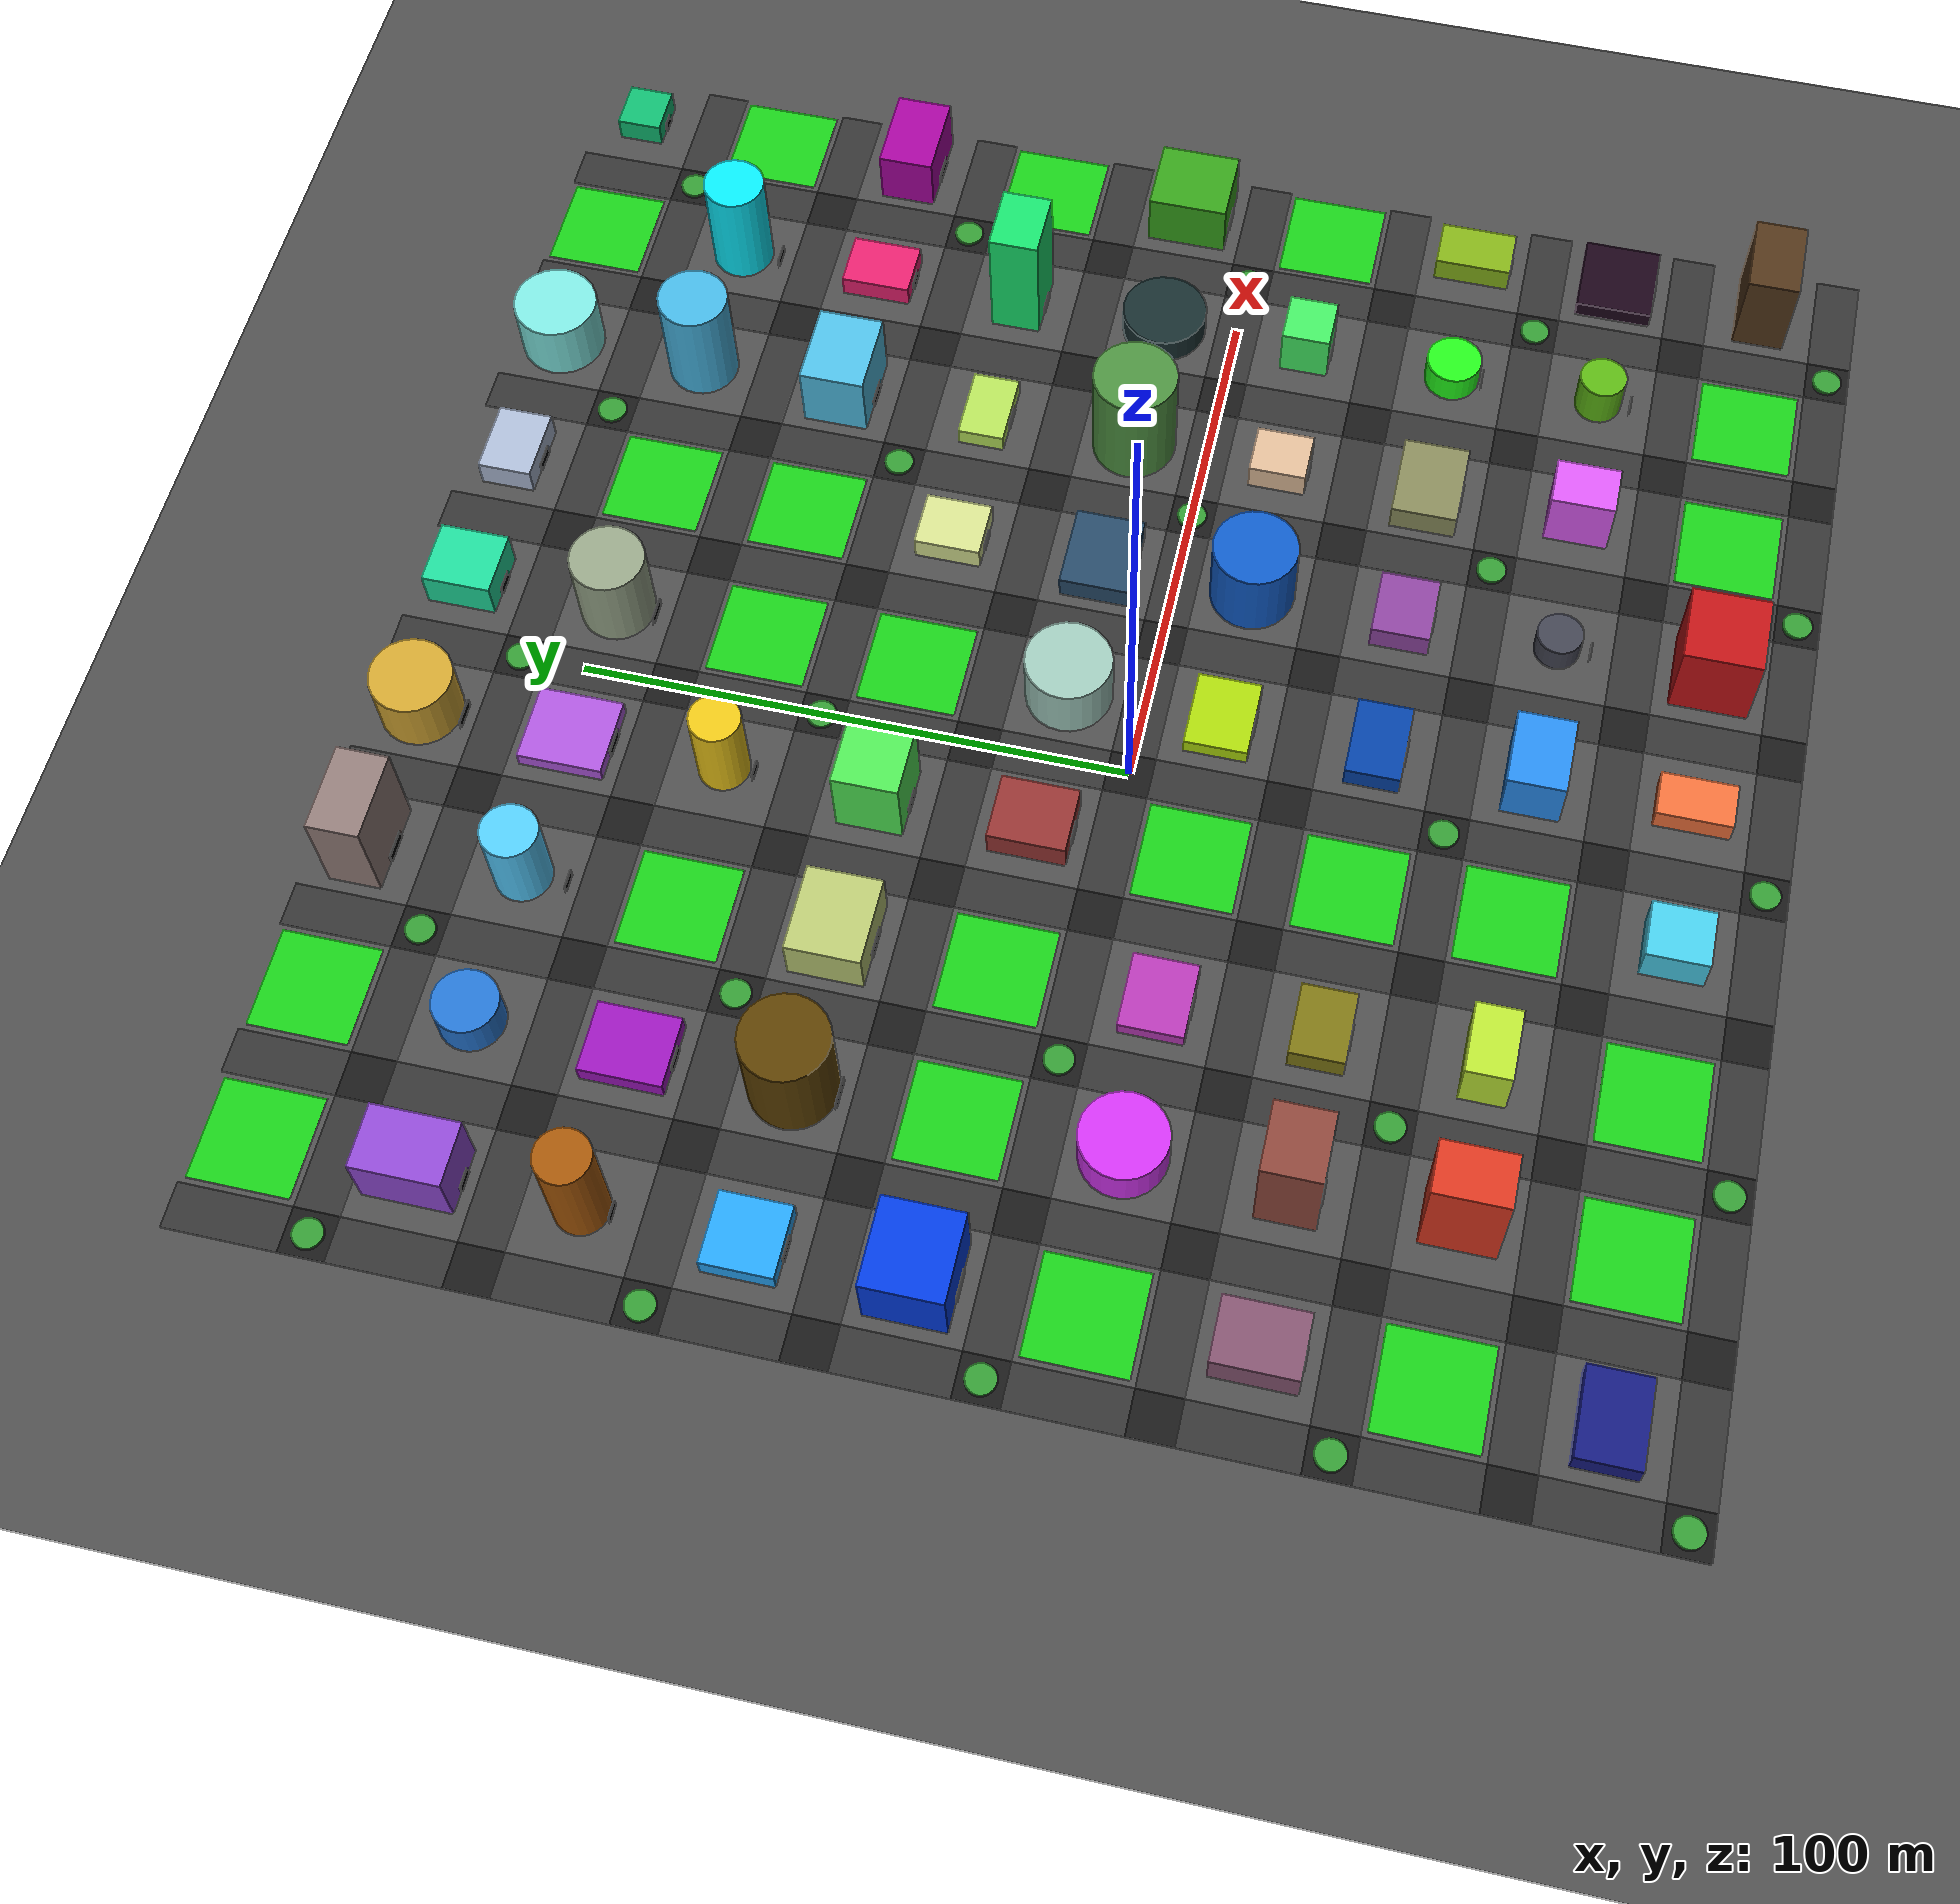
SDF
<?xml version="1.0" ?>
<sdf version="1.8">
  <world name="urban_city_rich">
    <physics name="1ms" type="ignored">
      <max_step_size>0.001</max_step_size>
      <real_time_factor>1.0</real_time_factor>
    </physics>
    <plugin filename="gz-sim-physics-system" name="gz::sim::systems::Physics"></plugin>
    <plugin filename="gz-sim-user-commands-system" name="gz::sim::systems::UserCommands"></plugin>
    <plugin filename="gz-sim-scene-broadcaster-system" name="gz::sim::systems::SceneBroadcaster"></plugin>
    <plugin filename="gz-sim-sensors-system" name="gz::sim::systems::Sensors">
        <render_engine>ogre2</render_engine>
    </plugin>
    <plugin filename="gz-sim-wind-effects-system" name="gz::sim::systems::WindEffects"></plugin>

    <light type="directional" name="sun">
      <cast_shadows>true</cast_shadows>
      <pose>0 0 10 0 0 0</pose>
      <diffuse>0.8 0.8 0.8 1</diffuse>
      <specular>0.2 0.2 0.2 1</specular>
      <direction>-0.5 0.1 -0.9</direction>
    </light>

    <model name="ground_plane">
      <static>true</static>
      <link name="link">
        <collision name="collision">
          <geometry><plane><normal>0 0 1</normal><size>200 200</size></plane></geometry>
          <surface>
            <friction>
              <ode>
                <mu>100</mu>
                <mu2>50</mu2>
              </ode>
            </friction>
          </surface>
        </collision>
        <visual name="visual">
          <geometry><plane><normal>0 0 1</normal><size>200 200</size></plane></geometry>
          <material><ambient>0.3 0.3 0.3 1</ambient><diffuse>0.3 0.3 0.3 1</diffuse></material>
        </visual>
      </link>
    </model>

    <model name="road_inter_-4_-4">
      <static>true</static>
      <pose>-112.0 -112.0 0.01 0 0 0</pose>
      <link name="link">
        <visual name="vis">
            <geometry><box><size>8.0 8.0 0.02</size></box></geometry>
            <material><ambient>0.1 0.1 0.1 1</ambient><diffuse>0.1 0.1 0.1 1</diffuse></material>
        </visual>
      </link>
    </model>

    <model name="roundabout_-4_-4">
      <static>true</static>
      <pose>-112.0 -112.0 0.3 0 0 0</pose>
      <link name="link">
        <collision name="col">
           <geometry><cylinder><radius>2.6666666666666665</radius><length>0.6</length></cylinder></geometry>
        </collision>
        <visual name="vis">
           <geometry><cylinder><radius>2.6666666666666665</radius><length>0.6</length></cylinder></geometry>
           <material><ambient>0.2 0.6 0.2 1</ambient><diffuse>0.2 0.6 0.2 1</diffuse></material>
        </visual>
      </link>
    </model>

    <model name="road_h_-4_-4">
      <static>true</static>
      <pose>-98.0 -112.0 0.01 0 0 0</pose>
      <link name="link">
        <visual name="vis">
            <geometry><box><size>20.0 8.0 0.02</size></box></geometry>
            <material><ambient>0.2 0.2 0.2 1</ambient><diffuse>0.2 0.2 0.2 1</diffuse></material>
        </visual>
      </link>
    </model>
    <model name="road_v_-4_-4">
      <static>true</static>
      <pose>-112.0 -98.0 0.01 0 0 0</pose>
      <link name="link">
        <visual name="vis">
            <geometry><box><size>8.0 20.0 0.02</size></box></geometry>
            <material><ambient>0.2 0.2 0.2 1</ambient><diffuse>0.2 0.2 0.2 1</diffuse></material>
        </visual>
      </link>
    </model>

    <model name="bldg_0">
      <static>true</static>
      <pose>-98.0 -98.0 2.5235670317674987 0 0 0</pose>
      <link name="link">
        <collision name="col">
           <geometry><box><size>15.342661748203877 11.08600410563863 5.0471340635349975</size></box></geometry>
        </collision>
        <visual name="vis">
           <geometry><box><size>15.342661748203877 11.08600410563863 5.0471340635349975</size></box></geometry>
           <material><ambient>0.07891768210494154 0.100371998829073 0.49105680813120545 1</ambient><diffuse>0.07891768210494154 0.100371998829073 0.49105680813120545 1</diffuse></material>
        </visual>
      </link>
    </model>

    <model name="door_0">
      <static>true</static>
      <pose>-98.0 -103.64300205281931 1.0 0 0 0</pose>
      <link name="link">
        <visual name="vis">
           <geometry><box><size>5.114220582734625 0.2 2.0</size></box></geometry>
           <material><ambient>0 0 0 1</ambient><diffuse>0 0 0 1</diffuse></material>
        </visual>
      </link>
    </model>

    <model name="road_inter_-4_-3">
      <static>true</static>
      <pose>-112.0 -84.0 0.01 0 0 0</pose>
      <link name="link">
        <visual name="vis">
            <geometry><box><size>8.0 8.0 0.02</size></box></geometry>
            <material><ambient>0.1 0.1 0.1 1</ambient><diffuse>0.1 0.1 0.1 1</diffuse></material>
        </visual>
      </link>
    </model>

    <model name="road_h_-4_-3">
      <static>true</static>
      <pose>-98.0 -84.0 0.01 0 0 0</pose>
      <link name="link">
        <visual name="vis">
            <geometry><box><size>20.0 8.0 0.02</size></box></geometry>
            <material><ambient>0.2 0.2 0.2 1</ambient><diffuse>0.2 0.2 0.2 1</diffuse></material>
        </visual>
      </link>
    </model>
    <model name="road_v_-4_-3">
      <static>true</static>
      <pose>-112.0 -70.0 0.01 0 0 0</pose>
      <link name="link">
        <visual name="vis">
            <geometry><box><size>8.0 20.0 0.02</size></box></geometry>
            <material><ambient>0.2 0.2 0.2 1</ambient><diffuse>0.2 0.2 0.2 1</diffuse></material>
        </visual>
      </link>
    </model>

    <model name="park_-4_-3">
      <static>true</static>
      <pose>-98.0 -70.0 0.05 0 0 0</pose>
      <link name="link">
        <visual name="vis">
            <geometry><box><size>18.0 18.0 0.1</size></box></geometry>
            <material><ambient>0.1 0.8 0.1 1</ambient><diffuse>0.1 0.8 0.1 1</diffuse></material>
        </visual>
      </link>
    </model>

    <model name="road_inter_-4_-2">
      <static>true</static>
      <pose>-112.0 -56.0 0.01 0 0 0</pose>
      <link name="link">
        <visual name="vis">
            <geometry><box><size>8.0 8.0 0.02</size></box></geometry>
            <material><ambient>0.1 0.1 0.1 1</ambient><diffuse>0.1 0.1 0.1 1</diffuse></material>
        </visual>
      </link>
    </model>

    <model name="roundabout_-4_-2">
      <static>true</static>
      <pose>-112.0 -56.0 0.3 0 0 0</pose>
      <link name="link">
        <collision name="col">
           <geometry><cylinder><radius>2.6666666666666665</radius><length>0.6</length></cylinder></geometry>
        </collision>
        <visual name="vis">
           <geometry><cylinder><radius>2.6666666666666665</radius><length>0.6</length></cylinder></geometry>
           <material><ambient>0.2 0.6 0.2 1</ambient><diffuse>0.2 0.6 0.2 1</diffuse></material>
        </visual>
      </link>
    </model>

    <model name="road_h_-4_-2">
      <static>true</static>
      <pose>-98.0 -56.0 0.01 0 0 0</pose>
      <link name="link">
        <visual name="vis">
            <geometry><box><size>20.0 8.0 0.02</size></box></geometry>
            <material><ambient>0.2 0.2 0.2 1</ambient><diffuse>0.2 0.2 0.2 1</diffuse></material>
        </visual>
      </link>
    </model>
    <model name="road_v_-4_-2">
      <static>true</static>
      <pose>-112.0 -42.0 0.01 0 0 0</pose>
      <link name="link">
        <visual name="vis">
            <geometry><box><size>8.0 20.0 0.02</size></box></geometry>
            <material><ambient>0.2 0.2 0.2 1</ambient><diffuse>0.2 0.2 0.2 1</diffuse></material>
        </visual>
      </link>
    </model>

    <model name="bldg_1">
      <static>true</static>
      <pose>-98.0 -42.0 3.6376901776272232 0 0 0</pose>
      <link name="link">
        <collision name="col">
           <geometry><box><size>11.35202361768915 14.776690094084369 7.2753803552544465</size></box></geometry>
        </collision>
        <visual name="vis">
           <geometry><box><size>11.35202361768915 14.776690094084369 7.2753803552544465</size></box></geometry>
           <material><ambient>0.5092049025601565 0.32316817157173483 0.43274199991856177 1</ambient><diffuse>0.5092049025601565 0.32316817157173483 0.43274199991856177 1</diffuse></material>
        </visual>
      </link>
    </model>

    <model name="door_1">
      <static>true</static>
      <pose>-98.0 -49.48834504704219 1.0 0 0 0</pose>
      <link name="link">
        <visual name="vis">
           <geometry><box><size>3.78400787256305 0.2 2.0</size></box></geometry>
           <material><ambient>0 0 0 1</ambient><diffuse>0 0 0 1</diffuse></material>
        </visual>
      </link>
    </model>

    <model name="road_inter_-4_-1">
      <static>true</static>
      <pose>-112.0 -28.0 0.01 0 0 0</pose>
      <link name="link">
        <visual name="vis">
            <geometry><box><size>8.0 8.0 0.02</size></box></geometry>
            <material><ambient>0.1 0.1 0.1 1</ambient><diffuse>0.1 0.1 0.1 1</diffuse></material>
        </visual>
      </link>
    </model>

    <model name="road_h_-4_-1">
      <static>true</static>
      <pose>-98.0 -28.0 0.01 0 0 0</pose>
      <link name="link">
        <visual name="vis">
            <geometry><box><size>20.0 8.0 0.02</size></box></geometry>
            <material><ambient>0.2 0.2 0.2 1</ambient><diffuse>0.2 0.2 0.2 1</diffuse></material>
        </visual>
      </link>
    </model>
    <model name="road_v_-4_-1">
      <static>true</static>
      <pose>-112.0 -14.0 0.01 0 0 0</pose>
      <link name="link">
        <visual name="vis">
            <geometry><box><size>8.0 20.0 0.02</size></box></geometry>
            <material><ambient>0.2 0.2 0.2 1</ambient><diffuse>0.2 0.2 0.2 1</diffuse></material>
        </visual>
      </link>
    </model>

    <model name="park_-4_-1">
      <static>true</static>
      <pose>-98.0 -14.0 0.05 0 0 0</pose>
      <link name="link">
        <visual name="vis">
            <geometry><box><size>18.0 18.0 0.1</size></box></geometry>
            <material><ambient>0.1 0.8 0.1 1</ambient><diffuse>0.1 0.8 0.1 1</diffuse></material>
        </visual>
      </link>
    </model>

    <model name="road_inter_-4_0">
      <static>true</static>
      <pose>-112.0 0.0 0.01 0 0 0</pose>
      <link name="link">
        <visual name="vis">
            <geometry><box><size>8.0 8.0 0.02</size></box></geometry>
            <material><ambient>0.1 0.1 0.1 1</ambient><diffuse>0.1 0.1 0.1 1</diffuse></material>
        </visual>
      </link>
    </model>

    <model name="roundabout_-4_0">
      <static>true</static>
      <pose>-112.0 0.0 0.3 0 0 0</pose>
      <link name="link">
        <collision name="col">
           <geometry><cylinder><radius>2.6666666666666665</radius><length>0.6</length></cylinder></geometry>
        </collision>
        <visual name="vis">
           <geometry><cylinder><radius>2.6666666666666665</radius><length>0.6</length></cylinder></geometry>
           <material><ambient>0.2 0.6 0.2 1</ambient><diffuse>0.2 0.6 0.2 1</diffuse></material>
        </visual>
      </link>
    </model>

    <model name="road_h_-4_0">
      <static>true</static>
      <pose>-98.0 0.0 0.01 0 0 0</pose>
      <link name="link">
        <visual name="vis">
            <geometry><box><size>20.0 8.0 0.02</size></box></geometry>
            <material><ambient>0.2 0.2 0.2 1</ambient><diffuse>0.2 0.2 0.2 1</diffuse></material>
        </visual>
      </link>
    </model>
    <model name="road_v_-4_0">
      <static>true</static>
      <pose>-112.0 14.0 0.01 0 0 0</pose>
      <link name="link">
        <visual name="vis">
            <geometry><box><size>8.0 20.0 0.02</size></box></geometry>
            <material><ambient>0.2 0.2 0.2 1</ambient><diffuse>0.2 0.2 0.2 1</diffuse></material>
        </visual>
      </link>
    </model>

    <model name="bldg_2">
      <static>true</static>
      <pose>-98.0 14.0 6.871921854589109 0 0 0</pose>
      <link name="link">
        <collision name="col">
           <geometry><box><size>15.495885785892245 14.268601737189726 13.743843709178218</size></box></geometry>
        </collision>
        <visual name="vis">
           <geometry><box><size>15.495885785892245 14.268601737189726 13.743843709178218</size></box></geometry>
           <material><ambient>0.007378564841799773 0.23080644680875095 0.8802637911668005 1</ambient><diffuse>0.007378564841799773 0.23080644680875095 0.8802637911668005 1</diffuse></material>
        </visual>
      </link>
    </model>

    <model name="door_2">
      <static>true</static>
      <pose>-98.0 6.765699131405137 1.0 0 0 0</pose>
      <link name="link">
        <visual name="vis">
           <geometry><box><size>5.165295261964082 0.2 2.0</size></box></geometry>
           <material><ambient>0 0 0 1</ambient><diffuse>0 0 0 1</diffuse></material>
        </visual>
      </link>
    </model>

    <model name="road_inter_-4_1">
      <static>true</static>
      <pose>-112.0 28.0 0.01 0 0 0</pose>
      <link name="link">
        <visual name="vis">
            <geometry><box><size>8.0 8.0 0.02</size></box></geometry>
            <material><ambient>0.1 0.1 0.1 1</ambient><diffuse>0.1 0.1 0.1 1</diffuse></material>
        </visual>
      </link>
    </model>

    <model name="road_h_-4_1">
      <static>true</static>
      <pose>-98.0 28.0 0.01 0 0 0</pose>
      <link name="link">
        <visual name="vis">
            <geometry><box><size>20.0 8.0 0.02</size></box></geometry>
            <material><ambient>0.2 0.2 0.2 1</ambient><diffuse>0.2 0.2 0.2 1</diffuse></material>
        </visual>
      </link>
    </model>
    <model name="road_v_-4_1">
      <static>true</static>
      <pose>-112.0 42.0 0.01 0 0 0</pose>
      <link name="link">
        <visual name="vis">
            <geometry><box><size>8.0 20.0 0.02</size></box></geometry>
            <material><ambient>0.2 0.2 0.2 1</ambient><diffuse>0.2 0.2 0.2 1</diffuse></material>
        </visual>
      </link>
    </model>

    <model name="bldg_3">
      <static>true</static>
      <pose>-98.0 42.0 2.091871394252661 0 0 0</pose>
      <link name="link">
        <collision name="col">
           <geometry><box><size>12.65519496365092 12.680258744932562 4.183742788505322</size></box></geometry>
        </collision>
        <visual name="vis">
           <geometry><box><size>12.65519496365092 12.680258744932562 4.183742788505322</size></box></geometry>
           <material><ambient>0.1498548266455363 0.6387725588322049 0.955054819178483 1</ambient><diffuse>0.1498548266455363 0.6387725588322049 0.955054819178483 1</diffuse></material>
        </visual>
      </link>
    </model>

    <model name="door_3">
      <static>true</static>
      <pose>-98.0 35.55987062753372 1.0 0 0 0</pose>
      <link name="link">
        <visual name="vis">
           <geometry><box><size>4.218398321216974 0.2 2.0</size></box></geometry>
           <material><ambient>0 0 0 1</ambient><diffuse>0 0 0 1</diffuse></material>
        </visual>
      </link>
    </model>

    <model name="road_inter_-4_2">
      <static>true</static>
      <pose>-112.0 56.0 0.01 0 0 0</pose>
      <link name="link">
        <visual name="vis">
            <geometry><box><size>8.0 8.0 0.02</size></box></geometry>
            <material><ambient>0.1 0.1 0.1 1</ambient><diffuse>0.1 0.1 0.1 1</diffuse></material>
        </visual>
      </link>
    </model>

    <model name="roundabout_-4_2">
      <static>true</static>
      <pose>-112.0 56.0 0.3 0 0 0</pose>
      <link name="link">
        <collision name="col">
           <geometry><cylinder><radius>2.6666666666666665</radius><length>0.6</length></cylinder></geometry>
        </collision>
        <visual name="vis">
           <geometry><cylinder><radius>2.6666666666666665</radius><length>0.6</length></cylinder></geometry>
           <material><ambient>0.2 0.6 0.2 1</ambient><diffuse>0.2 0.6 0.2 1</diffuse></material>
        </visual>
      </link>
    </model>

    <model name="road_h_-4_2">
      <static>true</static>
      <pose>-98.0 56.0 0.01 0 0 0</pose>
      <link name="link">
        <visual name="vis">
            <geometry><box><size>20.0 8.0 0.02</size></box></geometry>
            <material><ambient>0.2 0.2 0.2 1</ambient><diffuse>0.2 0.2 0.2 1</diffuse></material>
        </visual>
      </link>
    </model>
    <model name="road_v_-4_2">
      <static>true</static>
      <pose>-112.0 70.0 0.01 0 0 0</pose>
      <link name="link">
        <visual name="vis">
            <geometry><box><size>8.0 20.0 0.02</size></box></geometry>
            <material><ambient>0.2 0.2 0.2 1</ambient><diffuse>0.2 0.2 0.2 1</diffuse></material>
        </visual>
      </link>
    </model>

    <model name="bldg_4">
      <static>true</static>
      <pose>-98.0 70.0 11.17141163954446 0 0 0</pose>
      <link name="link">
        <collision name="col">
           <geometry><cylinder><radius>4.861963068080618</radius><length>22.34282327908892</length></cylinder></geometry>
        </collision>
        <visual name="vis">
           <geometry><cylinder><radius>4.861963068080618</radius><length>22.34282327908892</length></cylinder></geometry>
           <material><ambient>0.6452800324957052 0.34005277793005484 0.035646647061961856 1</ambient><diffuse>0.6452800324957052 0.34005277793005484 0.035646647061961856 1</diffuse></material>
        </visual>
      </link>
    </model>

    <model name="door_4">
      <static>true</static>
      <pose>-98.0 64.91522386664495 1.0 0 0 0</pose>
      <link name="link">
        <visual name="vis">
           <geometry><box><size>3.2413087120537454 0.2 2.0</size></box></geometry>
           <material><ambient>0 0 0 1</ambient><diffuse>0 0 0 1</diffuse></material>
        </visual>
      </link>
    </model>

    <model name="road_inter_-4_3">
      <static>true</static>
      <pose>-112.0 84.0 0.01 0 0 0</pose>
      <link name="link">
        <visual name="vis">
            <geometry><box><size>8.0 8.0 0.02</size></box></geometry>
            <material><ambient>0.1 0.1 0.1 1</ambient><diffuse>0.1 0.1 0.1 1</diffuse></material>
        </visual>
      </link>
    </model>

    <model name="road_h_-4_3">
      <static>true</static>
      <pose>-98.0 84.0 0.01 0 0 0</pose>
      <link name="link">
        <visual name="vis">
            <geometry><box><size>20.0 8.0 0.02</size></box></geometry>
            <material><ambient>0.2 0.2 0.2 1</ambient><diffuse>0.2 0.2 0.2 1</diffuse></material>
        </visual>
      </link>
    </model>
    <model name="road_v_-4_3">
      <static>true</static>
      <pose>-112.0 98.0 0.01 0 0 0</pose>
      <link name="link">
        <visual name="vis">
            <geometry><box><size>8.0 20.0 0.02</size></box></geometry>
            <material><ambient>0.2 0.2 0.2 1</ambient><diffuse>0.2 0.2 0.2 1</diffuse></material>
        </visual>
      </link>
    </model>

    <model name="bldg_5">
      <static>true</static>
      <pose>-98.0 98.0 6.102142837959303 0 0 0</pose>
      <link name="link">
        <collision name="col">
           <geometry><box><size>11.222737588818491 15.767643930074145 12.204285675918605</size></box></geometry>
        </collision>
        <visual name="vis">
           <geometry><box><size>11.222737588818491 15.767643930074145 12.204285675918605</size></box></geometry>
           <material><ambient>0.5592032974253442 0.2837923102071037 0.8228978980625674 1</ambient><diffuse>0.5592032974253442 0.2837923102071037 0.8228978980625674 1</diffuse></material>
        </visual>
      </link>
    </model>

    <model name="door_5">
      <static>true</static>
      <pose>-98.0 90.01617803496293 1.0 0 0 0</pose>
      <link name="link">
        <visual name="vis">
           <geometry><box><size>3.7409125296061636 0.2 2.0</size></box></geometry>
           <material><ambient>0 0 0 1</ambient><diffuse>0 0 0 1</diffuse></material>
        </visual>
      </link>
    </model>

    <model name="road_inter_-4_4">
      <static>true</static>
      <pose>-112.0 112.0 0.01 0 0 0</pose>
      <link name="link">
        <visual name="vis">
            <geometry><box><size>8.0 8.0 0.02</size></box></geometry>
            <material><ambient>0.1 0.1 0.1 1</ambient><diffuse>0.1 0.1 0.1 1</diffuse></material>
        </visual>
      </link>
    </model>

    <model name="roundabout_-4_4">
      <static>true</static>
      <pose>-112.0 112.0 0.3 0 0 0</pose>
      <link name="link">
        <collision name="col">
           <geometry><cylinder><radius>2.6666666666666665</radius><length>0.6</length></cylinder></geometry>
        </collision>
        <visual name="vis">
           <geometry><cylinder><radius>2.6666666666666665</radius><length>0.6</length></cylinder></geometry>
           <material><ambient>0.2 0.6 0.2 1</ambient><diffuse>0.2 0.6 0.2 1</diffuse></material>
        </visual>
      </link>
    </model>

    <model name="road_h_-4_4">
      <static>true</static>
      <pose>-98.0 112.0 0.01 0 0 0</pose>
      <link name="link">
        <visual name="vis">
            <geometry><box><size>20.0 8.0 0.02</size></box></geometry>
            <material><ambient>0.2 0.2 0.2 1</ambient><diffuse>0.2 0.2 0.2 1</diffuse></material>
        </visual>
      </link>
    </model>
    <model name="road_v_-4_4">
      <static>true</static>
      <pose>-112.0 126.0 0.01 0 0 0</pose>
      <link name="link">
        <visual name="vis">
            <geometry><box><size>8.0 20.0 0.02</size></box></geometry>
            <material><ambient>0.2 0.2 0.2 1</ambient><diffuse>0.2 0.2 0.2 1</diffuse></material>
        </visual>
      </link>
    </model>

    <model name="park_-4_4">
      <static>true</static>
      <pose>-98.0 126.0 0.05 0 0 0</pose>
      <link name="link">
        <visual name="vis">
            <geometry><box><size>18.0 18.0 0.1</size></box></geometry>
            <material><ambient>0.1 0.8 0.1 1</ambient><diffuse>0.1 0.8 0.1 1</diffuse></material>
        </visual>
      </link>
    </model>

    <model name="road_inter_-3_-4">
      <static>true</static>
      <pose>-84.0 -112.0 0.01 0 0 0</pose>
      <link name="link">
        <visual name="vis">
            <geometry><box><size>8.0 8.0 0.02</size></box></geometry>
            <material><ambient>0.1 0.1 0.1 1</ambient><diffuse>0.1 0.1 0.1 1</diffuse></material>
        </visual>
      </link>
    </model>

    <model name="road_h_-3_-4">
      <static>true</static>
      <pose>-70.0 -112.0 0.01 0 0 0</pose>
      <link name="link">
        <visual name="vis">
            <geometry><box><size>20.0 8.0 0.02</size></box></geometry>
            <material><ambient>0.2 0.2 0.2 1</ambient><diffuse>0.2 0.2 0.2 1</diffuse></material>
        </visual>
      </link>
    </model>
    <model name="road_v_-3_-4">
      <static>true</static>
      <pose>-84.0 -98.0 0.01 0 0 0</pose>
      <link name="link">
        <visual name="vis">
            <geometry><box><size>8.0 20.0 0.02</size></box></geometry>
            <material><ambient>0.2 0.2 0.2 1</ambient><diffuse>0.2 0.2 0.2 1</diffuse></material>
        </visual>
      </link>
    </model>

    <model name="park_-3_-4">
      <static>true</static>
      <pose>-70.0 -98.0 0.05 0 0 0</pose>
      <link name="link">
        <visual name="vis">
            <geometry><box><size>18.0 18.0 0.1</size></box></geometry>
            <material><ambient>0.1 0.8 0.1 1</ambient><diffuse>0.1 0.8 0.1 1</diffuse></material>
        </visual>
      </link>
    </model>

    <model name="road_inter_-3_-3">
      <static>true</static>
      <pose>-84.0 -84.0 0.01 0 0 0</pose>
      <link name="link">
        <visual name="vis">
            <geometry><box><size>8.0 8.0 0.02</size></box></geometry>
            <material><ambient>0.1 0.1 0.1 1</ambient><diffuse>0.1 0.1 0.1 1</diffuse></material>
        </visual>
      </link>
    </model>

    <model name="road_h_-3_-3">
      <static>true</static>
      <pose>-70.0 -84.0 0.01 0 0 0</pose>
      <link name="link">
        <visual name="vis">
            <geometry><box><size>20.0 8.0 0.02</size></box></geometry>
            <material><ambient>0.2 0.2 0.2 1</ambient><diffuse>0.2 0.2 0.2 1</diffuse></material>
        </visual>
      </link>
    </model>
    <model name="road_v_-3_-3">
      <static>true</static>
      <pose>-84.0 -70.0 0.01 0 0 0</pose>
      <link name="link">
        <visual name="vis">
            <geometry><box><size>8.0 20.0 0.02</size></box></geometry>
            <material><ambient>0.2 0.2 0.2 1</ambient><diffuse>0.2 0.2 0.2 1</diffuse></material>
        </visual>
      </link>
    </model>

    <model name="bldg_6">
      <static>true</static>
      <pose>-70.0 -70.0 11.145302864680088 0 0 0</pose>
      <link name="link">
        <collision name="col">
           <geometry><box><size>9.249776720305364 13.105119866609332 22.290605729360177</size></box></geometry>
        </collision>
        <visual name="vis">
           <geometry><box><size>9.249776720305364 13.105119866609332 22.290605729360177</size></box></geometry>
           <material><ambient>0.8486679505580024 0.21356448876894685 0.12262370836348857 1</ambient><diffuse>0.8486679505580024 0.21356448876894685 0.12262370836348857 1</diffuse></material>
        </visual>
      </link>
    </model>

    <model name="door_6">
      <static>true</static>
      <pose>-70.0 -76.65255993330466 1.0 0 0 0</pose>
      <link name="link">
        <visual name="vis">
           <geometry><box><size>3.083258906768455 0.2 2.0</size></box></geometry>
           <material><ambient>0 0 0 1</ambient><diffuse>0 0 0 1</diffuse></material>
        </visual>
      </link>
    </model>

    <model name="road_inter_-3_-2">
      <static>true</static>
      <pose>-84.0 -56.0 0.01 0 0 0</pose>
      <link name="link">
        <visual name="vis">
            <geometry><box><size>8.0 8.0 0.02</size></box></geometry>
            <material><ambient>0.1 0.1 0.1 1</ambient><diffuse>0.1 0.1 0.1 1</diffuse></material>
        </visual>
      </link>
    </model>

    <model name="road_h_-3_-2">
      <static>true</static>
      <pose>-70.0 -56.0 0.01 0 0 0</pose>
      <link name="link">
        <visual name="vis">
            <geometry><box><size>20.0 8.0 0.02</size></box></geometry>
            <material><ambient>0.2 0.2 0.2 1</ambient><diffuse>0.2 0.2 0.2 1</diffuse></material>
        </visual>
      </link>
    </model>
    <model name="road_v_-3_-2">
      <static>true</static>
      <pose>-84.0 -42.0 0.01 0 0 0</pose>
      <link name="link">
        <visual name="vis">
            <geometry><box><size>8.0 20.0 0.02</size></box></geometry>
            <material><ambient>0.2 0.2 0.2 1</ambient><diffuse>0.2 0.2 0.2 1</diffuse></material>
        </visual>
      </link>
    </model>

    <model name="bldg_7">
      <static>true</static>
      <pose>-70.0 -42.0 10.33584450808003 0 0 0</pose>
      <link name="link">
        <collision name="col">
           <geometry><box><size>12.347266834379655 10.477315987206403 20.67168901616006</size></box></geometry>
        </collision>
        <visual name="vis">
           <geometry><box><size>12.347266834379655 10.477315987206403 20.67168901616006</size></box></geometry>
           <material><ambient>0.5452253943904294 0.27323704681909844 0.22826414803682094 1</ambient><diffuse>0.5452253943904294 0.27323704681909844 0.22826414803682094 1</diffuse></material>
        </visual>
      </link>
    </model>

    <model name="door_7">
      <static>true</static>
      <pose>-70.0 -47.3386579936032 1.0 0 0 0</pose>
      <link name="link">
        <visual name="vis">
           <geometry><box><size>4.1157556114598846 0.2 2.0</size></box></geometry>
           <material><ambient>0 0 0 1</ambient><diffuse>0 0 0 1</diffuse></material>
        </visual>
      </link>
    </model>

    <model name="road_inter_-3_-1">
      <static>true</static>
      <pose>-84.0 -28.0 0.01 0 0 0</pose>
      <link name="link">
        <visual name="vis">
            <geometry><box><size>8.0 8.0 0.02</size></box></geometry>
            <material><ambient>0.1 0.1 0.1 1</ambient><diffuse>0.1 0.1 0.1 1</diffuse></material>
        </visual>
      </link>
    </model>

    <model name="road_h_-3_-1">
      <static>true</static>
      <pose>-70.0 -28.0 0.01 0 0 0</pose>
      <link name="link">
        <visual name="vis">
            <geometry><box><size>20.0 8.0 0.02</size></box></geometry>
            <material><ambient>0.2 0.2 0.2 1</ambient><diffuse>0.2 0.2 0.2 1</diffuse></material>
        </visual>
      </link>
    </model>
    <model name="road_v_-3_-1">
      <static>true</static>
      <pose>-84.0 -14.0 0.01 0 0 0</pose>
      <link name="link">
        <visual name="vis">
            <geometry><box><size>8.0 20.0 0.02</size></box></geometry>
            <material><ambient>0.2 0.2 0.2 1</ambient><diffuse>0.2 0.2 0.2 1</diffuse></material>
        </visual>
      </link>
    </model>

    <model name="bldg_8">
      <static>true</static>
      <pose>-70.0 -14.0 4.16093976846412 0 0 0</pose>
      <link name="link">
        <collision name="col">
           <geometry><cylinder><radius>7.724120574102244</radius><length>8.32187953692824</length></cylinder></geometry>
        </collision>
        <visual name="vis">
           <geometry><cylinder><radius>7.724120574102244</radius><length>8.32187953692824</length></cylinder></geometry>
           <material><ambient>0.8154843360258764 0.20335821501575657 0.9309179945168319 1</ambient><diffuse>0.8154843360258764 0.20335821501575657 0.9309179945168319 1</diffuse></material>
        </visual>
      </link>
    </model>

    <model name="door_8">
      <static>true</static>
      <pose>-70.0 -19.347105833627378 1.0 0 0 0</pose>
      <link name="link">
        <visual name="vis">
           <geometry><box><size>5.149413716068163 0.2 2.0</size></box></geometry>
           <material><ambient>0 0 0 1</ambient><diffuse>0 0 0 1</diffuse></material>
        </visual>
      </link>
    </model>

    <model name="road_inter_-3_0">
      <static>true</static>
      <pose>-84.0 0.0 0.01 0 0 0</pose>
      <link name="link">
        <visual name="vis">
            <geometry><box><size>8.0 8.0 0.02</size></box></geometry>
            <material><ambient>0.1 0.1 0.1 1</ambient><diffuse>0.1 0.1 0.1 1</diffuse></material>
        </visual>
      </link>
    </model>

    <model name="road_h_-3_0">
      <static>true</static>
      <pose>-70.0 0.0 0.01 0 0 0</pose>
      <link name="link">
        <visual name="vis">
            <geometry><box><size>20.0 8.0 0.02</size></box></geometry>
            <material><ambient>0.2 0.2 0.2 1</ambient><diffuse>0.2 0.2 0.2 1</diffuse></material>
        </visual>
      </link>
    </model>
    <model name="road_v_-3_0">
      <static>true</static>
      <pose>-84.0 14.0 0.01 0 0 0</pose>
      <link name="link">
        <visual name="vis">
            <geometry><box><size>8.0 20.0 0.02</size></box></geometry>
            <material><ambient>0.2 0.2 0.2 1</ambient><diffuse>0.2 0.2 0.2 1</diffuse></material>
        </visual>
      </link>
    </model>

    <model name="park_-3_0">
      <static>true</static>
      <pose>-70.0 14.0 0.05 0 0 0</pose>
      <link name="link">
        <visual name="vis">
            <geometry><box><size>18.0 18.0 0.1</size></box></geometry>
            <material><ambient>0.1 0.8 0.1 1</ambient><diffuse>0.1 0.8 0.1 1</diffuse></material>
        </visual>
      </link>
    </model>

    <model name="road_inter_-3_1">
      <static>true</static>
      <pose>-84.0 28.0 0.01 0 0 0</pose>
      <link name="link">
        <visual name="vis">
            <geometry><box><size>8.0 8.0 0.02</size></box></geometry>
            <material><ambient>0.1 0.1 0.1 1</ambient><diffuse>0.1 0.1 0.1 1</diffuse></material>
        </visual>
      </link>
    </model>

    <model name="road_h_-3_1">
      <static>true</static>
      <pose>-70.0 28.0 0.01 0 0 0</pose>
      <link name="link">
        <visual name="vis">
            <geometry><box><size>20.0 8.0 0.02</size></box></geometry>
            <material><ambient>0.2 0.2 0.2 1</ambient><diffuse>0.2 0.2 0.2 1</diffuse></material>
        </visual>
      </link>
    </model>
    <model name="road_v_-3_1">
      <static>true</static>
      <pose>-84.0 42.0 0.01 0 0 0</pose>
      <link name="link">
        <visual name="vis">
            <geometry><box><size>8.0 20.0 0.02</size></box></geometry>
            <material><ambient>0.2 0.2 0.2 1</ambient><diffuse>0.2 0.2 0.2 1</diffuse></material>
        </visual>
      </link>
    </model>

    <model name="bldg_9">
      <static>true</static>
      <pose>-70.0 42.0 9.960052538225515 0 0 0</pose>
      <link name="link">
        <collision name="col">
           <geometry><cylinder><radius>7.8172579100735575</radius><length>19.92010507645103</length></cylinder></geometry>
        </collision>
        <visual name="vis">
           <geometry><cylinder><radius>7.8172579100735575</radius><length>19.92010507645103</length></cylinder></geometry>
           <material><ambient>0.3586243095088105 0.24959450865288613 0.012275405890124547 1</ambient><diffuse>0.3586243095088105 0.24959450865288613 0.012275405890124547 1</diffuse></material>
        </visual>
      </link>
    </model>

    <model name="door_9">
      <static>true</static>
      <pose>-70.0 34.14622287364215 1.0 0 0 0</pose>
      <link name="link">
        <visual name="vis">
           <geometry><box><size>5.211505273382372 0.2 2.0</size></box></geometry>
           <material><ambient>0 0 0 1</ambient><diffuse>0 0 0 1</diffuse></material>
        </visual>
      </link>
    </model>

    <model name="road_inter_-3_2">
      <static>true</static>
      <pose>-84.0 56.0 0.01 0 0 0</pose>
      <link name="link">
        <visual name="vis">
            <geometry><box><size>8.0 8.0 0.02</size></box></geometry>
            <material><ambient>0.1 0.1 0.1 1</ambient><diffuse>0.1 0.1 0.1 1</diffuse></material>
        </visual>
      </link>
    </model>

    <model name="road_h_-3_2">
      <static>true</static>
      <pose>-70.0 56.0 0.01 0 0 0</pose>
      <link name="link">
        <visual name="vis">
            <geometry><box><size>20.0 8.0 0.02</size></box></geometry>
            <material><ambient>0.2 0.2 0.2 1</ambient><diffuse>0.2 0.2 0.2 1</diffuse></material>
        </visual>
      </link>
    </model>
    <model name="road_v_-3_2">
      <static>true</static>
      <pose>-84.0 70.0 0.01 0 0 0</pose>
      <link name="link">
        <visual name="vis">
            <geometry><box><size>8.0 20.0 0.02</size></box></geometry>
            <material><ambient>0.2 0.2 0.2 1</ambient><diffuse>0.2 0.2 0.2 1</diffuse></material>
        </visual>
      </link>
    </model>

    <model name="bldg_10">
      <static>true</static>
      <pose>-70.0 70.0 1.8771646480618858 0 0 0</pose>
      <link name="link">
        <collision name="col">
           <geometry><box><size>12.654126522715291 14.81363523251945 3.7543292961237715</size></box></geometry>
        </collision>
        <visual name="vis">
           <geometry><box><size>12.654126522715291 14.81363523251945 3.7543292961237715</size></box></geometry>
           <material><ambient>0.6026039844535511 0.08320478289895294 0.7268993759771187 1</ambient><diffuse>0.6026039844535511 0.08320478289895294 0.7268993759771187 1</diffuse></material>
        </visual>
      </link>
    </model>

    <model name="door_10">
      <static>true</static>
      <pose>-70.0 62.493182383740276 1.0 0 0 0</pose>
      <link name="link">
        <visual name="vis">
           <geometry><box><size>4.21804217423843 0.2 2.0</size></box></geometry>
           <material><ambient>0 0 0 1</ambient><diffuse>0 0 0 1</diffuse></material>
        </visual>
      </link>
    </model>

    <model name="road_inter_-3_3">
      <static>true</static>
      <pose>-84.0 84.0 0.01 0 0 0</pose>
      <link name="link">
        <visual name="vis">
            <geometry><box><size>8.0 8.0 0.02</size></box></geometry>
            <material><ambient>0.1 0.1 0.1 1</ambient><diffuse>0.1 0.1 0.1 1</diffuse></material>
        </visual>
      </link>
    </model>

    <model name="road_h_-3_3">
      <static>true</static>
      <pose>-70.0 84.0 0.01 0 0 0</pose>
      <link name="link">
        <visual name="vis">
            <geometry><box><size>20.0 8.0 0.02</size></box></geometry>
            <material><ambient>0.2 0.2 0.2 1</ambient><diffuse>0.2 0.2 0.2 1</diffuse></material>
        </visual>
      </link>
    </model>
    <model name="road_v_-3_3">
      <static>true</static>
      <pose>-84.0 98.0 0.01 0 0 0</pose>
      <link name="link">
        <visual name="vis">
            <geometry><box><size>8.0 20.0 0.02</size></box></geometry>
            <material><ambient>0.2 0.2 0.2 1</ambient><diffuse>0.2 0.2 0.2 1</diffuse></material>
        </visual>
      </link>
    </model>

    <model name="bldg_11">
      <static>true</static>
      <pose>-70.0 98.0 3.8265298128650302 0 0 0</pose>
      <link name="link">
        <collision name="col">
           <geometry><cylinder><radius>5.824363381465605</radius><length>7.6530596257300605</length></cylinder></geometry>
        </collision>
        <visual name="vis">
           <geometry><cylinder><radius>5.824363381465605</radius><length>7.6530596257300605</length></cylinder></geometry>
           <material><ambient>0.14358297201273418 0.4594956118217749 0.818678515794683 1</ambient><diffuse>0.14358297201273418 0.4594956118217749 0.818678515794683 1</diffuse></material>
        </visual>
      </link>
    </model>

    <model name="door_11">
      <static>true</static>
      <pose>-70.0 93.88478456954448 1.0 0 0 0</pose>
      <link name="link">
        <visual name="vis">
           <geometry><box><size>3.8829089209770697 0.2 2.0</size></box></geometry>
           <material><ambient>0 0 0 1</ambient><diffuse>0 0 0 1</diffuse></material>
        </visual>
      </link>
    </model>

    <model name="road_inter_-3_4">
      <static>true</static>
      <pose>-84.0 112.0 0.01 0 0 0</pose>
      <link name="link">
        <visual name="vis">
            <geometry><box><size>8.0 8.0 0.02</size></box></geometry>
            <material><ambient>0.1 0.1 0.1 1</ambient><diffuse>0.1 0.1 0.1 1</diffuse></material>
        </visual>
      </link>
    </model>

    <model name="road_h_-3_4">
      <static>true</static>
      <pose>-70.0 112.0 0.01 0 0 0</pose>
      <link name="link">
        <visual name="vis">
            <geometry><box><size>20.0 8.0 0.02</size></box></geometry>
            <material><ambient>0.2 0.2 0.2 1</ambient><diffuse>0.2 0.2 0.2 1</diffuse></material>
        </visual>
      </link>
    </model>
    <model name="road_v_-3_4">
      <static>true</static>
      <pose>-84.0 126.0 0.01 0 0 0</pose>
      <link name="link">
        <visual name="vis">
            <geometry><box><size>8.0 20.0 0.02</size></box></geometry>
            <material><ambient>0.2 0.2 0.2 1</ambient><diffuse>0.2 0.2 0.2 1</diffuse></material>
        </visual>
      </link>
    </model>

    <model name="park_-3_4">
      <static>true</static>
      <pose>-70.0 126.0 0.05 0 0 0</pose>
      <link name="link">
        <visual name="vis">
            <geometry><box><size>18.0 18.0 0.1</size></box></geometry>
            <material><ambient>0.1 0.8 0.1 1</ambient><diffuse>0.1 0.8 0.1 1</diffuse></material>
        </visual>
      </link>
    </model>

    <model name="road_inter_-2_-4">
      <static>true</static>
      <pose>-56.0 -112.0 0.01 0 0 0</pose>
      <link name="link">
        <visual name="vis">
            <geometry><box><size>8.0 8.0 0.02</size></box></geometry>
            <material><ambient>0.1 0.1 0.1 1</ambient><diffuse>0.1 0.1 0.1 1</diffuse></material>
        </visual>
      </link>
    </model>

    <model name="roundabout_-2_-4">
      <static>true</static>
      <pose>-56.0 -112.0 0.3 0 0 0</pose>
      <link name="link">
        <collision name="col">
           <geometry><cylinder><radius>2.6666666666666665</radius><length>0.6</length></cylinder></geometry>
        </collision>
        <visual name="vis">
           <geometry><cylinder><radius>2.6666666666666665</radius><length>0.6</length></cylinder></geometry>
           <material><ambient>0.2 0.6 0.2 1</ambient><diffuse>0.2 0.6 0.2 1</diffuse></material>
        </visual>
      </link>
    </model>

    <model name="road_h_-2_-4">
      <static>true</static>
      <pose>-42.0 -112.0 0.01 0 0 0</pose>
      <link name="link">
        <visual name="vis">
            <geometry><box><size>20.0 8.0 0.02</size></box></geometry>
            <material><ambient>0.2 0.2 0.2 1</ambient><diffuse>0.2 0.2 0.2 1</diffuse></material>
        </visual>
      </link>
    </model>
    <model name="road_v_-2_-4">
      <static>true</static>
      <pose>-56.0 -98.0 0.01 0 0 0</pose>
      <link name="link">
        <visual name="vis">
            <geometry><box><size>8.0 20.0 0.02</size></box></geometry>
            <material><ambient>0.2 0.2 0.2 1</ambient><diffuse>0.2 0.2 0.2 1</diffuse></material>
        </visual>
      </link>
    </model>

    <model name="park_-2_-4">
      <static>true</static>
      <pose>-42.0 -98.0 0.05 0 0 0</pose>
      <link name="link">
        <visual name="vis">
            <geometry><box><size>18.0 18.0 0.1</size></box></geometry>
            <material><ambient>0.1 0.8 0.1 1</ambient><diffuse>0.1 0.8 0.1 1</diffuse></material>
        </visual>
      </link>
    </model>

    <model name="road_inter_-2_-3">
      <static>true</static>
      <pose>-56.0 -84.0 0.01 0 0 0</pose>
      <link name="link">
        <visual name="vis">
            <geometry><box><size>8.0 8.0 0.02</size></box></geometry>
            <material><ambient>0.1 0.1 0.1 1</ambient><diffuse>0.1 0.1 0.1 1</diffuse></material>
        </visual>
      </link>
    </model>

    <model name="road_h_-2_-3">
      <static>true</static>
      <pose>-42.0 -84.0 0.01 0 0 0</pose>
      <link name="link">
        <visual name="vis">
            <geometry><box><size>20.0 8.0 0.02</size></box></geometry>
            <material><ambient>0.2 0.2 0.2 1</ambient><diffuse>0.2 0.2 0.2 1</diffuse></material>
        </visual>
      </link>
    </model>
    <model name="road_v_-2_-3">
      <static>true</static>
      <pose>-56.0 -70.0 0.01 0 0 0</pose>
      <link name="link">
        <visual name="vis">
            <geometry><box><size>8.0 20.0 0.02</size></box></geometry>
            <material><ambient>0.2 0.2 0.2 1</ambient><diffuse>0.2 0.2 0.2 1</diffuse></material>
        </visual>
      </link>
    </model>

    <model name="bldg_12">
      <static>true</static>
      <pose>-42.0 -70.0 5.734184694096465 0 0 0</pose>
      <link name="link">
        <collision name="col">
           <geometry><box><size>12.679352574609744 8.170057510644643 11.46836938819293</size></box></geometry>
        </collision>
        <visual name="vis">
           <geometry><box><size>12.679352574609744 8.170057510644643 11.46836938819293</size></box></geometry>
           <material><ambient>0.724466864392436 0.8841149506035106 0.2005147474207506 1</ambient><diffuse>0.724466864392436 0.8841149506035106 0.2005147474207506 1</diffuse></material>
        </visual>
      </link>
    </model>

    <model name="door_12">
      <static>true</static>
      <pose>-42.0 -74.18502875532232 1.0 0 0 0</pose>
      <link name="link">
        <visual name="vis">
           <geometry><box><size>4.226450858203248 0.2 2.0</size></box></geometry>
           <material><ambient>0 0 0 1</ambient><diffuse>0 0 0 1</diffuse></material>
        </visual>
      </link>
    </model>

    <model name="road_inter_-2_-2">
      <static>true</static>
      <pose>-56.0 -56.0 0.01 0 0 0</pose>
      <link name="link">
        <visual name="vis">
            <geometry><box><size>8.0 8.0 0.02</size></box></geometry>
            <material><ambient>0.1 0.1 0.1 1</ambient><diffuse>0.1 0.1 0.1 1</diffuse></material>
        </visual>
      </link>
    </model>

    <model name="roundabout_-2_-2">
      <static>true</static>
      <pose>-56.0 -56.0 0.3 0 0 0</pose>
      <link name="link">
        <collision name="col">
           <geometry><cylinder><radius>2.6666666666666665</radius><length>0.6</length></cylinder></geometry>
        </collision>
        <visual name="vis">
           <geometry><cylinder><radius>2.6666666666666665</radius><length>0.6</length></cylinder></geometry>
           <material><ambient>0.2 0.6 0.2 1</ambient><diffuse>0.2 0.6 0.2 1</diffuse></material>
        </visual>
      </link>
    </model>

    <model name="road_h_-2_-2">
      <static>true</static>
      <pose>-42.0 -56.0 0.01 0 0 0</pose>
      <link name="link">
        <visual name="vis">
            <geometry><box><size>20.0 8.0 0.02</size></box></geometry>
            <material><ambient>0.2 0.2 0.2 1</ambient><diffuse>0.2 0.2 0.2 1</diffuse></material>
        </visual>
      </link>
    </model>
    <model name="road_v_-2_-2">
      <static>true</static>
      <pose>-56.0 -42.0 0.01 0 0 0</pose>
      <link name="link">
        <visual name="vis">
            <geometry><box><size>8.0 20.0 0.02</size></box></geometry>
            <material><ambient>0.2 0.2 0.2 1</ambient><diffuse>0.2 0.2 0.2 1</diffuse></material>
        </visual>
      </link>
    </model>

    <model name="bldg_13">
      <static>true</static>
      <pose>-42.0 -42.0 2.522974517584019 0 0 0</pose>
      <link name="link">
        <collision name="col">
           <geometry><box><size>12.931677133729247 9.709780513660842 5.045949035168038</size></box></geometry>
        </collision>
        <visual name="vis">
           <geometry><box><size>12.931677133729247 9.709780513660842 5.045949035168038</size></box></geometry>
           <material><ambient>0.48810979955961264 0.45837308282455147 0.07947602669510367 1</ambient><diffuse>0.48810979955961264 0.45837308282455147 0.07947602669510367 1</diffuse></material>
        </visual>
      </link>
    </model>

    <model name="door_13">
      <static>true</static>
      <pose>-42.0 -46.954890256830424 1.0 0 0 0</pose>
      <link name="link">
        <visual name="vis">
           <geometry><box><size>4.310559044576416 0.2 2.0</size></box></geometry>
           <material><ambient>0 0 0 1</ambient><diffuse>0 0 0 1</diffuse></material>
        </visual>
      </link>
    </model>

    <model name="road_inter_-2_-1">
      <static>true</static>
      <pose>-56.0 -28.0 0.01 0 0 0</pose>
      <link name="link">
        <visual name="vis">
            <geometry><box><size>8.0 8.0 0.02</size></box></geometry>
            <material><ambient>0.1 0.1 0.1 1</ambient><diffuse>0.1 0.1 0.1 1</diffuse></material>
        </visual>
      </link>
    </model>

    <model name="road_h_-2_-1">
      <static>true</static>
      <pose>-42.0 -28.0 0.01 0 0 0</pose>
      <link name="link">
        <visual name="vis">
            <geometry><box><size>20.0 8.0 0.02</size></box></geometry>
            <material><ambient>0.2 0.2 0.2 1</ambient><diffuse>0.2 0.2 0.2 1</diffuse></material>
        </visual>
      </link>
    </model>
    <model name="road_v_-2_-1">
      <static>true</static>
      <pose>-56.0 -14.0 0.01 0 0 0</pose>
      <link name="link">
        <visual name="vis">
            <geometry><box><size>8.0 20.0 0.02</size></box></geometry>
            <material><ambient>0.2 0.2 0.2 1</ambient><diffuse>0.2 0.2 0.2 1</diffuse></material>
        </visual>
      </link>
    </model>

    <model name="bldg_14">
      <static>true</static>
      <pose>-42.0 -14.0 1.5267114841007532 0 0 0</pose>
      <link name="link">
        <collision name="col">
           <geometry><box><size>13.632911136492433 11.555225343470225 3.0534229682015064</size></box></geometry>
        </collision>
        <visual name="vis">
           <geometry><box><size>13.632911136492433 11.555225343470225 3.0534229682015064</size></box></geometry>
           <material><ambient>0.7042233576448294 0.21905984064392303 0.6998118177265623 1</ambient><diffuse>0.7042233576448294 0.21905984064392303 0.6998118177265623 1</diffuse></material>
        </visual>
      </link>
    </model>

    <model name="door_14">
      <static>true</static>
      <pose>-42.0 -19.877612671735115 1.0 0 0 0</pose>
      <link name="link">
        <visual name="vis">
           <geometry><box><size>4.544303712164145 0.2 2.0</size></box></geometry>
           <material><ambient>0 0 0 1</ambient><diffuse>0 0 0 1</diffuse></material>
        </visual>
      </link>
    </model>

    <model name="road_inter_-2_0">
      <static>true</static>
      <pose>-56.0 0.0 0.01 0 0 0</pose>
      <link name="link">
        <visual name="vis">
            <geometry><box><size>8.0 8.0 0.02</size></box></geometry>
            <material><ambient>0.1 0.1 0.1 1</ambient><diffuse>0.1 0.1 0.1 1</diffuse></material>
        </visual>
      </link>
    </model>

    <model name="roundabout_-2_0">
      <static>true</static>
      <pose>-56.0 0.0 0.3 0 0 0</pose>
      <link name="link">
        <collision name="col">
           <geometry><cylinder><radius>2.6666666666666665</radius><length>0.6</length></cylinder></geometry>
        </collision>
        <visual name="vis">
           <geometry><cylinder><radius>2.6666666666666665</radius><length>0.6</length></cylinder></geometry>
           <material><ambient>0.2 0.6 0.2 1</ambient><diffuse>0.2 0.6 0.2 1</diffuse></material>
        </visual>
      </link>
    </model>

    <model name="road_h_-2_0">
      <static>true</static>
      <pose>-42.0 0.0 0.01 0 0 0</pose>
      <link name="link">
        <visual name="vis">
            <geometry><box><size>20.0 8.0 0.02</size></box></geometry>
            <material><ambient>0.2 0.2 0.2 1</ambient><diffuse>0.2 0.2 0.2 1</diffuse></material>
        </visual>
      </link>
    </model>
    <model name="road_v_-2_0">
      <static>true</static>
      <pose>-56.0 14.0 0.01 0 0 0</pose>
      <link name="link">
        <visual name="vis">
            <geometry><box><size>8.0 20.0 0.02</size></box></geometry>
            <material><ambient>0.2 0.2 0.2 1</ambient><diffuse>0.2 0.2 0.2 1</diffuse></material>
        </visual>
      </link>
    </model>

    <model name="park_-2_0">
      <static>true</static>
      <pose>-42.0 14.0 0.05 0 0 0</pose>
      <link name="link">
        <visual name="vis">
            <geometry><box><size>18.0 18.0 0.1</size></box></geometry>
            <material><ambient>0.1 0.8 0.1 1</ambient><diffuse>0.1 0.8 0.1 1</diffuse></material>
        </visual>
      </link>
    </model>

    <model name="road_inter_-2_1">
      <static>true</static>
      <pose>-56.0 28.0 0.01 0 0 0</pose>
      <link name="link">
        <visual name="vis">
            <geometry><box><size>8.0 8.0 0.02</size></box></geometry>
            <material><ambient>0.1 0.1 0.1 1</ambient><diffuse>0.1 0.1 0.1 1</diffuse></material>
        </visual>
      </link>
    </model>

    <model name="road_h_-2_1">
      <static>true</static>
      <pose>-42.0 28.0 0.01 0 0 0</pose>
      <link name="link">
        <visual name="vis">
            <geometry><box><size>20.0 8.0 0.02</size></box></geometry>
            <material><ambient>0.2 0.2 0.2 1</ambient><diffuse>0.2 0.2 0.2 1</diffuse></material>
        </visual>
      </link>
    </model>
    <model name="road_v_-2_1">
      <static>true</static>
      <pose>-56.0 42.0 0.01 0 0 0</pose>
      <link name="link">
        <visual name="vis">
            <geometry><box><size>8.0 20.0 0.02</size></box></geometry>
            <material><ambient>0.2 0.2 0.2 1</ambient><diffuse>0.2 0.2 0.2 1</diffuse></material>
        </visual>
      </link>
    </model>

    <model name="bldg_15">
      <static>true</static>
      <pose>-42.0 42.0 4.647097805640947 0 0 0</pose>
      <link name="link">
        <collision name="col">
           <geometry><box><size>15.76349798601867 13.472286385605344 9.294195611281895</size></box></geometry>
        </collision>
        <visual name="vis">
           <geometry><box><size>15.76349798601867 13.472286385605344 9.294195611281895</size></box></geometry>
           <material><ambient>0.7191576907212245 0.7760415757399151 0.4462818985575434 1</ambient><diffuse>0.7191576907212245 0.7760415757399151 0.4462818985575434 1</diffuse></material>
        </visual>
      </link>
    </model>

    <model name="door_15">
      <static>true</static>
      <pose>-42.0 35.16385680719733 1.0 0 0 0</pose>
      <link name="link">
        <visual name="vis">
           <geometry><box><size>5.25449932867289 0.2 2.0</size></box></geometry>
           <material><ambient>0 0 0 1</ambient><diffuse>0 0 0 1</diffuse></material>
        </visual>
      </link>
    </model>

    <model name="road_inter_-2_2">
      <static>true</static>
      <pose>-56.0 56.0 0.01 0 0 0</pose>
      <link name="link">
        <visual name="vis">
            <geometry><box><size>8.0 8.0 0.02</size></box></geometry>
            <material><ambient>0.1 0.1 0.1 1</ambient><diffuse>0.1 0.1 0.1 1</diffuse></material>
        </visual>
      </link>
    </model>

    <model name="roundabout_-2_2">
      <static>true</static>
      <pose>-56.0 56.0 0.3 0 0 0</pose>
      <link name="link">
        <collision name="col">
           <geometry><cylinder><radius>2.6666666666666665</radius><length>0.6</length></cylinder></geometry>
        </collision>
        <visual name="vis">
           <geometry><cylinder><radius>2.6666666666666665</radius><length>0.6</length></cylinder></geometry>
           <material><ambient>0.2 0.6 0.2 1</ambient><diffuse>0.2 0.6 0.2 1</diffuse></material>
        </visual>
      </link>
    </model>

    <model name="road_h_-2_2">
      <static>true</static>
      <pose>-42.0 56.0 0.01 0 0 0</pose>
      <link name="link">
        <visual name="vis">
            <geometry><box><size>20.0 8.0 0.02</size></box></geometry>
            <material><ambient>0.2 0.2 0.2 1</ambient><diffuse>0.2 0.2 0.2 1</diffuse></material>
        </visual>
      </link>
    </model>
    <model name="road_v_-2_2">
      <static>true</static>
      <pose>-56.0 70.0 0.01 0 0 0</pose>
      <link name="link">
        <visual name="vis">
            <geometry><box><size>8.0 20.0 0.02</size></box></geometry>
            <material><ambient>0.2 0.2 0.2 1</ambient><diffuse>0.2 0.2 0.2 1</diffuse></material>
        </visual>
      </link>
    </model>

    <model name="park_-2_2">
      <static>true</static>
      <pose>-42.0 70.0 0.05 0 0 0</pose>
      <link name="link">
        <visual name="vis">
            <geometry><box><size>18.0 18.0 0.1</size></box></geometry>
            <material><ambient>0.1 0.8 0.1 1</ambient><diffuse>0.1 0.8 0.1 1</diffuse></material>
        </visual>
      </link>
    </model>

    <model name="road_inter_-2_3">
      <static>true</static>
      <pose>-56.0 84.0 0.01 0 0 0</pose>
      <link name="link">
        <visual name="vis">
            <geometry><box><size>8.0 8.0 0.02</size></box></geometry>
            <material><ambient>0.1 0.1 0.1 1</ambient><diffuse>0.1 0.1 0.1 1</diffuse></material>
        </visual>
      </link>
    </model>

    <model name="road_h_-2_3">
      <static>true</static>
      <pose>-42.0 84.0 0.01 0 0 0</pose>
      <link name="link">
        <visual name="vis">
            <geometry><box><size>20.0 8.0 0.02</size></box></geometry>
            <material><ambient>0.2 0.2 0.2 1</ambient><diffuse>0.2 0.2 0.2 1</diffuse></material>
        </visual>
      </link>
    </model>
    <model name="road_v_-2_3">
      <static>true</static>
      <pose>-56.0 98.0 0.01 0 0 0</pose>
      <link name="link">
        <visual name="vis">
            <geometry><box><size>8.0 20.0 0.02</size></box></geometry>
            <material><ambient>0.2 0.2 0.2 1</ambient><diffuse>0.2 0.2 0.2 1</diffuse></material>
        </visual>
      </link>
    </model>

    <model name="bldg_16">
      <static>true</static>
      <pose>-42.0 98.0 8.187884358222295 0 0 0</pose>
      <link name="link">
        <collision name="col">
           <geometry><cylinder><radius>5.1270535653662455</radius><length>16.37576871644459</length></cylinder></geometry>
        </collision>
        <visual name="vis">
           <geometry><cylinder><radius>5.1270535653662455</radius><length>16.37576871644459</length></cylinder></geometry>
           <material><ambient>0.32547679088761305 0.7877283173419841 0.9836225916744558 1</ambient><diffuse>0.32547679088761305 0.7877283173419841 0.9836225916744558 1</diffuse></material>
        </visual>
      </link>
    </model>

    <model name="door_16">
      <static>true</static>
      <pose>-42.0 89.93933041101761 1.0 0 0 0</pose>
      <link name="link">
        <visual name="vis">
           <geometry><box><size>3.4180357102441636 0.2 2.0</size></box></geometry>
           <material><ambient>0 0 0 1</ambient><diffuse>0 0 0 1</diffuse></material>
        </visual>
      </link>
    </model>

    <model name="road_inter_-2_4">
      <static>true</static>
      <pose>-56.0 112.0 0.01 0 0 0</pose>
      <link name="link">
        <visual name="vis">
            <geometry><box><size>8.0 8.0 0.02</size></box></geometry>
            <material><ambient>0.1 0.1 0.1 1</ambient><diffuse>0.1 0.1 0.1 1</diffuse></material>
        </visual>
      </link>
    </model>

    <model name="roundabout_-2_4">
      <static>true</static>
      <pose>-56.0 112.0 0.3 0 0 0</pose>
      <link name="link">
        <collision name="col">
           <geometry><cylinder><radius>2.6666666666666665</radius><length>0.6</length></cylinder></geometry>
        </collision>
        <visual name="vis">
           <geometry><cylinder><radius>2.6666666666666665</radius><length>0.6</length></cylinder></geometry>
           <material><ambient>0.2 0.6 0.2 1</ambient><diffuse>0.2 0.6 0.2 1</diffuse></material>
        </visual>
      </link>
    </model>

    <model name="road_h_-2_4">
      <static>true</static>
      <pose>-42.0 112.0 0.01 0 0 0</pose>
      <link name="link">
        <visual name="vis">
            <geometry><box><size>20.0 8.0 0.02</size></box></geometry>
            <material><ambient>0.2 0.2 0.2 1</ambient><diffuse>0.2 0.2 0.2 1</diffuse></material>
        </visual>
      </link>
    </model>
    <model name="road_v_-2_4">
      <static>true</static>
      <pose>-56.0 126.0 0.01 0 0 0</pose>
      <link name="link">
        <visual name="vis">
            <geometry><box><size>8.0 20.0 0.02</size></box></geometry>
            <material><ambient>0.2 0.2 0.2 1</ambient><diffuse>0.2 0.2 0.2 1</diffuse></material>
        </visual>
      </link>
    </model>

    <model name="bldg_17">
      <static>true</static>
      <pose>-42.0 126.0 9.525055032280763 0 0 0</pose>
      <link name="link">
        <collision name="col">
           <geometry><box><size>15.701362822979156 9.450235959792298 19.050110064561526</size></box></geometry>
        </collision>
        <visual name="vis">
           <geometry><box><size>15.701362822979156 9.450235959792298 19.050110064561526</size></box></geometry>
           <material><ambient>0.5679989177881775 0.4847383450541677 0.4688976092850521 1</ambient><diffuse>0.5679989177881775 0.4847383450541677 0.4688976092850521 1</diffuse></material>
        </visual>
      </link>
    </model>

    <model name="door_17">
      <static>true</static>
      <pose>-42.0 121.17488202010385 1.0 0 0 0</pose>
      <link name="link">
        <visual name="vis">
           <geometry><box><size>5.2337876076597185 0.2 2.0</size></box></geometry>
           <material><ambient>0 0 0 1</ambient><diffuse>0 0 0 1</diffuse></material>
        </visual>
      </link>
    </model>

    <model name="road_inter_-1_-4">
      <static>true</static>
      <pose>-28.0 -112.0 0.01 0 0 0</pose>
      <link name="link">
        <visual name="vis">
            <geometry><box><size>8.0 8.0 0.02</size></box></geometry>
            <material><ambient>0.1 0.1 0.1 1</ambient><diffuse>0.1 0.1 0.1 1</diffuse></material>
        </visual>
      </link>
    </model>

    <model name="road_h_-1_-4">
      <static>true</static>
      <pose>-14.0 -112.0 0.01 0 0 0</pose>
      <link name="link">
        <visual name="vis">
            <geometry><box><size>20.0 8.0 0.02</size></box></geometry>
            <material><ambient>0.2 0.2 0.2 1</ambient><diffuse>0.2 0.2 0.2 1</diffuse></material>
        </visual>
      </link>
    </model>
    <model name="road_v_-1_-4">
      <static>true</static>
      <pose>-28.0 -98.0 0.01 0 0 0</pose>
      <link name="link">
        <visual name="vis">
            <geometry><box><size>8.0 20.0 0.02</size></box></geometry>
            <material><ambient>0.2 0.2 0.2 1</ambient><diffuse>0.2 0.2 0.2 1</diffuse></material>
        </visual>
      </link>
    </model>

    <model name="bldg_18">
      <static>true</static>
      <pose>-14.0 -98.0 3.8560939050084353 0 0 0</pose>
      <link name="link">
        <collision name="col">
           <geometry><box><size>10.253962400846973 11.17725089507213 7.712187810016871</size></box></geometry>
        </collision>
        <visual name="vis">
           <geometry><box><size>10.253962400846973 11.17725089507213 7.712187810016871</size></box></geometry>
           <material><ambient>0.2759380565349887 0.791651058803078 0.898773091240485 1</ambient><diffuse>0.2759380565349887 0.791651058803078 0.898773091240485 1</diffuse></material>
        </visual>
      </link>
    </model>

    <model name="door_18">
      <static>true</static>
      <pose>-14.0 -103.68862544753605 1.0 0 0 0</pose>
      <link name="link">
        <visual name="vis">
           <geometry><box><size>3.417987466948991 0.2 2.0</size></box></geometry>
           <material><ambient>0 0 0 1</ambient><diffuse>0 0 0 1</diffuse></material>
        </visual>
      </link>
    </model>

    <model name="road_inter_-1_-3">
      <static>true</static>
      <pose>-28.0 -84.0 0.01 0 0 0</pose>
      <link name="link">
        <visual name="vis">
            <geometry><box><size>8.0 8.0 0.02</size></box></geometry>
            <material><ambient>0.1 0.1 0.1 1</ambient><diffuse>0.1 0.1 0.1 1</diffuse></material>
        </visual>
      </link>
    </model>

    <model name="road_h_-1_-3">
      <static>true</static>
      <pose>-14.0 -84.0 0.01 0 0 0</pose>
      <link name="link">
        <visual name="vis">
            <geometry><box><size>20.0 8.0 0.02</size></box></geometry>
            <material><ambient>0.2 0.2 0.2 1</ambient><diffuse>0.2 0.2 0.2 1</diffuse></material>
        </visual>
      </link>
    </model>
    <model name="road_v_-1_-3">
      <static>true</static>
      <pose>-28.0 -70.0 0.01 0 0 0</pose>
      <link name="link">
        <visual name="vis">
            <geometry><box><size>8.0 20.0 0.02</size></box></geometry>
            <material><ambient>0.2 0.2 0.2 1</ambient><diffuse>0.2 0.2 0.2 1</diffuse></material>
        </visual>
      </link>
    </model>

    <model name="park_-1_-3">
      <static>true</static>
      <pose>-14.0 -70.0 0.05 0 0 0</pose>
      <link name="link">
        <visual name="vis">
            <geometry><box><size>18.0 18.0 0.1</size></box></geometry>
            <material><ambient>0.1 0.8 0.1 1</ambient><diffuse>0.1 0.8 0.1 1</diffuse></material>
        </visual>
      </link>
    </model>

    <model name="road_inter_-1_-2">
      <static>true</static>
      <pose>-28.0 -56.0 0.01 0 0 0</pose>
      <link name="link">
        <visual name="vis">
            <geometry><box><size>8.0 8.0 0.02</size></box></geometry>
            <material><ambient>0.1 0.1 0.1 1</ambient><diffuse>0.1 0.1 0.1 1</diffuse></material>
        </visual>
      </link>
    </model>

    <model name="road_h_-1_-2">
      <static>true</static>
      <pose>-14.0 -56.0 0.01 0 0 0</pose>
      <link name="link">
        <visual name="vis">
            <geometry><box><size>20.0 8.0 0.02</size></box></geometry>
            <material><ambient>0.2 0.2 0.2 1</ambient><diffuse>0.2 0.2 0.2 1</diffuse></material>
        </visual>
      </link>
    </model>
    <model name="road_v_-1_-2">
      <static>true</static>
      <pose>-28.0 -42.0 0.01 0 0 0</pose>
      <link name="link">
        <visual name="vis">
            <geometry><box><size>8.0 20.0 0.02</size></box></geometry>
            <material><ambient>0.2 0.2 0.2 1</ambient><diffuse>0.2 0.2 0.2 1</diffuse></material>
        </visual>
      </link>
    </model>

    <model name="park_-1_-2">
      <static>true</static>
      <pose>-14.0 -42.0 0.05 0 0 0</pose>
      <link name="link">
        <visual name="vis">
            <geometry><box><size>18.0 18.0 0.1</size></box></geometry>
            <material><ambient>0.1 0.8 0.1 1</ambient><diffuse>0.1 0.8 0.1 1</diffuse></material>
        </visual>
      </link>
    </model>

    <model name="road_inter_-1_-1">
      <static>true</static>
      <pose>-28.0 -28.0 0.01 0 0 0</pose>
      <link name="link">
        <visual name="vis">
            <geometry><box><size>8.0 8.0 0.02</size></box></geometry>
            <material><ambient>0.1 0.1 0.1 1</ambient><diffuse>0.1 0.1 0.1 1</diffuse></material>
        </visual>
      </link>
    </model>

    <model name="road_h_-1_-1">
      <static>true</static>
      <pose>-14.0 -28.0 0.01 0 0 0</pose>
      <link name="link">
        <visual name="vis">
            <geometry><box><size>20.0 8.0 0.02</size></box></geometry>
            <material><ambient>0.2 0.2 0.2 1</ambient><diffuse>0.2 0.2 0.2 1</diffuse></material>
        </visual>
      </link>
    </model>
    <model name="road_v_-1_-1">
      <static>true</static>
      <pose>-28.0 -14.0 0.01 0 0 0</pose>
      <link name="link">
        <visual name="vis">
            <geometry><box><size>8.0 20.0 0.02</size></box></geometry>
            <material><ambient>0.2 0.2 0.2 1</ambient><diffuse>0.2 0.2 0.2 1</diffuse></material>
        </visual>
      </link>
    </model>

    <model name="park_-1_-1">
      <static>true</static>
      <pose>-14.0 -14.0 0.05 0 0 0</pose>
      <link name="link">
        <visual name="vis">
            <geometry><box><size>18.0 18.0 0.1</size></box></geometry>
            <material><ambient>0.1 0.8 0.1 1</ambient><diffuse>0.1 0.8 0.1 1</diffuse></material>
        </visual>
      </link>
    </model>

    <model name="road_inter_-1_0">
      <static>true</static>
      <pose>-28.0 0.0 0.01 0 0 0</pose>
      <link name="link">
        <visual name="vis">
            <geometry><box><size>8.0 8.0 0.02</size></box></geometry>
            <material><ambient>0.1 0.1 0.1 1</ambient><diffuse>0.1 0.1 0.1 1</diffuse></material>
        </visual>
      </link>
    </model>

    <model name="road_h_-1_0">
      <static>true</static>
      <pose>-14.0 0.0 0.01 0 0 0</pose>
      <link name="link">
        <visual name="vis">
            <geometry><box><size>20.0 8.0 0.02</size></box></geometry>
            <material><ambient>0.2 0.2 0.2 1</ambient><diffuse>0.2 0.2 0.2 1</diffuse></material>
        </visual>
      </link>
    </model>
    <model name="road_v_-1_0">
      <static>true</static>
      <pose>-28.0 14.0 0.01 0 0 0</pose>
      <link name="link">
        <visual name="vis">
            <geometry><box><size>8.0 20.0 0.02</size></box></geometry>
            <material><ambient>0.2 0.2 0.2 1</ambient><diffuse>0.2 0.2 0.2 1</diffuse></material>
        </visual>
      </link>
    </model>

    <model name="bldg_19">
      <static>true</static>
      <pose>-14.0 14.0 2.757713768041565 0 0 0</pose>
      <link name="link">
        <collision name="col">
           <geometry><box><size>12.140478911146484 14.036751003596061 5.51542753608313</size></box></geometry>
        </collision>
        <visual name="vis">
           <geometry><box><size>12.140478911146484 14.036751003596061 5.51542753608313</size></box></geometry>
           <material><ambient>0.5731753270957767 0.2038373489023103 0.19605695629109343 1</ambient><diffuse>0.5731753270957767 0.2038373489023103 0.19605695629109343 1</diffuse></material>
        </visual>
      </link>
    </model>

    <model name="door_19">
      <static>true</static>
      <pose>-14.0 6.88162449820197 1.0 0 0 0</pose>
      <link name="link">
        <visual name="vis">
           <geometry><box><size>4.046826303715495 0.2 2.0</size></box></geometry>
           <material><ambient>0 0 0 1</ambient><diffuse>0 0 0 1</diffuse></material>
        </visual>
      </link>
    </model>

    <model name="road_inter_-1_1">
      <static>true</static>
      <pose>-28.0 28.0 0.01 0 0 0</pose>
      <link name="link">
        <visual name="vis">
            <geometry><box><size>8.0 8.0 0.02</size></box></geometry>
            <material><ambient>0.1 0.1 0.1 1</ambient><diffuse>0.1 0.1 0.1 1</diffuse></material>
        </visual>
      </link>
    </model>

    <model name="road_h_-1_1">
      <static>true</static>
      <pose>-14.0 28.0 0.01 0 0 0</pose>
      <link name="link">
        <visual name="vis">
            <geometry><box><size>20.0 8.0 0.02</size></box></geometry>
            <material><ambient>0.2 0.2 0.2 1</ambient><diffuse>0.2 0.2 0.2 1</diffuse></material>
        </visual>
      </link>
    </model>
    <model name="road_v_-1_1">
      <static>true</static>
      <pose>-28.0 42.0 0.01 0 0 0</pose>
      <link name="link">
        <visual name="vis">
            <geometry><box><size>8.0 20.0 0.02</size></box></geometry>
            <material><ambient>0.2 0.2 0.2 1</ambient><diffuse>0.2 0.2 0.2 1</diffuse></material>
        </visual>
      </link>
    </model>

    <model name="bldg_20">
      <static>true</static>
      <pose>-14.0 42.0 7.672740519004155 0 0 0</pose>
      <link name="link">
        <collision name="col">
           <geometry><box><size>12.881039106564529 11.936921281808964 15.34548103800831</size></box></geometry>
        </collision>
        <visual name="vis">
           <geometry><box><size>12.881039106564529 11.936921281808964 15.34548103800831</size></box></geometry>
           <material><ambient>0.3089189860773851 0.8969932661377837 0.3322621758122244 1</ambient><diffuse>0.3089189860773851 0.8969932661377837 0.3322621758122244 1</diffuse></material>
        </visual>
      </link>
    </model>

    <model name="door_20">
      <static>true</static>
      <pose>-14.0 35.93153935909552 1.0 0 0 0</pose>
      <link name="link">
        <visual name="vis">
           <geometry><box><size>4.293679702188176 0.2 2.0</size></box></geometry>
           <material><ambient>0 0 0 1</ambient><diffuse>0 0 0 1</diffuse></material>
        </visual>
      </link>
    </model>

    <model name="road_inter_-1_2">
      <static>true</static>
      <pose>-28.0 56.0 0.01 0 0 0</pose>
      <link name="link">
        <visual name="vis">
            <geometry><box><size>8.0 8.0 0.02</size></box></geometry>
            <material><ambient>0.1 0.1 0.1 1</ambient><diffuse>0.1 0.1 0.1 1</diffuse></material>
        </visual>
      </link>
    </model>

    <model name="road_h_-1_2">
      <static>true</static>
      <pose>-14.0 56.0 0.01 0 0 0</pose>
      <link name="link">
        <visual name="vis">
            <geometry><box><size>20.0 8.0 0.02</size></box></geometry>
            <material><ambient>0.2 0.2 0.2 1</ambient><diffuse>0.2 0.2 0.2 1</diffuse></material>
        </visual>
      </link>
    </model>
    <model name="road_v_-1_2">
      <static>true</static>
      <pose>-28.0 70.0 0.01 0 0 0</pose>
      <link name="link">
        <visual name="vis">
            <geometry><box><size>8.0 20.0 0.02</size></box></geometry>
            <material><ambient>0.2 0.2 0.2 1</ambient><diffuse>0.2 0.2 0.2 1</diffuse></material>
        </visual>
      </link>
    </model>

    <model name="bldg_21">
      <static>true</static>
      <pose>-14.0 70.0 8.666523748330219 0 0 0</pose>
      <link name="link">
        <collision name="col">
           <geometry><cylinder><radius>4.649175699969307</radius><length>17.333047496660438</length></cylinder></geometry>
        </collision>
        <visual name="vis">
           <geometry><cylinder><radius>4.649175699969307</radius><length>17.333047496660438</length></cylinder></geometry>
           <material><ambient>0.9140545132175812 0.7648078160391948 0.09196075143216109 1</ambient><diffuse>0.9140545132175812 0.7648078160391948 0.09196075143216109 1</diffuse></material>
        </visual>
      </link>
    </model>

    <model name="door_21">
      <static>true</static>
      <pose>-14.0 64.47551798296992 1.0 0 0 0</pose>
      <link name="link">
        <visual name="vis">
           <geometry><box><size>3.099450466646205 0.2 2.0</size></box></geometry>
           <material><ambient>0 0 0 1</ambient><diffuse>0 0 0 1</diffuse></material>
        </visual>
      </link>
    </model>

    <model name="road_inter_-1_3">
      <static>true</static>
      <pose>-28.0 84.0 0.01 0 0 0</pose>
      <link name="link">
        <visual name="vis">
            <geometry><box><size>8.0 8.0 0.02</size></box></geometry>
            <material><ambient>0.1 0.1 0.1 1</ambient><diffuse>0.1 0.1 0.1 1</diffuse></material>
        </visual>
      </link>
    </model>

    <model name="road_h_-1_3">
      <static>true</static>
      <pose>-14.0 84.0 0.01 0 0 0</pose>
      <link name="link">
        <visual name="vis">
            <geometry><box><size>20.0 8.0 0.02</size></box></geometry>
            <material><ambient>0.2 0.2 0.2 1</ambient><diffuse>0.2 0.2 0.2 1</diffuse></material>
        </visual>
      </link>
    </model>
    <model name="road_v_-1_3">
      <static>true</static>
      <pose>-28.0 98.0 0.01 0 0 0</pose>
      <link name="link">
        <visual name="vis">
            <geometry><box><size>8.0 20.0 0.02</size></box></geometry>
            <material><ambient>0.2 0.2 0.2 1</ambient><diffuse>0.2 0.2 0.2 1</diffuse></material>
        </visual>
      </link>
    </model>

    <model name="bldg_22">
      <static>true</static>
      <pose>-14.0 98.0 1.5162245402027925 0 0 0</pose>
      <link name="link">
        <collision name="col">
           <geometry><box><size>14.177328477459566 15.376592342885587 3.032449080405585</size></box></geometry>
        </collision>
        <visual name="vis">
           <geometry><box><size>14.177328477459566 15.376592342885587 3.032449080405585</size></box></geometry>
           <material><ambient>0.6715406523524126 0.3362186619153813 0.853923451624441 1</ambient><diffuse>0.6715406523524126 0.3362186619153813 0.853923451624441 1</diffuse></material>
        </visual>
      </link>
    </model>

    <model name="door_22">
      <static>true</static>
      <pose>-14.0 90.2117038285572 1.0 0 0 0</pose>
      <link name="link">
        <visual name="vis">
           <geometry><box><size>4.725776159153189 0.2 2.0</size></box></geometry>
           <material><ambient>0 0 0 1</ambient><diffuse>0 0 0 1</diffuse></material>
        </visual>
      </link>
    </model>

    <model name="road_inter_-1_4">
      <static>true</static>
      <pose>-28.0 112.0 0.01 0 0 0</pose>
      <link name="link">
        <visual name="vis">
            <geometry><box><size>8.0 8.0 0.02</size></box></geometry>
            <material><ambient>0.1 0.1 0.1 1</ambient><diffuse>0.1 0.1 0.1 1</diffuse></material>
        </visual>
      </link>
    </model>

    <model name="road_h_-1_4">
      <static>true</static>
      <pose>-14.0 112.0 0.01 0 0 0</pose>
      <link name="link">
        <visual name="vis">
            <geometry><box><size>20.0 8.0 0.02</size></box></geometry>
            <material><ambient>0.2 0.2 0.2 1</ambient><diffuse>0.2 0.2 0.2 1</diffuse></material>
        </visual>
      </link>
    </model>
    <model name="road_v_-1_4">
      <static>true</static>
      <pose>-28.0 126.0 0.01 0 0 0</pose>
      <link name="link">
        <visual name="vis">
            <geometry><box><size>8.0 20.0 0.02</size></box></geometry>
            <material><ambient>0.2 0.2 0.2 1</ambient><diffuse>0.2 0.2 0.2 1</diffuse></material>
        </visual>
      </link>
    </model>

    <model name="bldg_23">
      <static>true</static>
      <pose>-14.0 126.0 5.76797907140169 0 0 0</pose>
      <link name="link">
        <collision name="col">
           <geometry><cylinder><radius>7.475280069416048</radius><length>11.53595814280338</length></cylinder></geometry>
        </collision>
        <visual name="vis">
           <geometry><cylinder><radius>7.475280069416048</radius><length>11.53595814280338</length></cylinder></geometry>
           <material><ambient>0.8143191471643694 0.643111451474141 0.1933663860682776 1</ambient><diffuse>0.8143191471643694 0.643111451474141 0.1933663860682776 1</diffuse></material>
        </visual>
      </link>
    </model>

    <model name="door_23">
      <static>true</static>
      <pose>-14.0 117.99811806132087 1.0 0 0 0</pose>
      <link name="link">
        <visual name="vis">
           <geometry><box><size>4.9835200462773654 0.2 2.0</size></box></geometry>
           <material><ambient>0 0 0 1</ambient><diffuse>0 0 0 1</diffuse></material>
        </visual>
      </link>
    </model>

    <model name="road_inter_0_-4">
      <static>true</static>
      <pose>0.0 -112.0 0.01 0 0 0</pose>
      <link name="link">
        <visual name="vis">
            <geometry><box><size>8.0 8.0 0.02</size></box></geometry>
            <material><ambient>0.1 0.1 0.1 1</ambient><diffuse>0.1 0.1 0.1 1</diffuse></material>
        </visual>
      </link>
    </model>

    <model name="roundabout_0_-4">
      <static>true</static>
      <pose>0.0 -112.0 0.3 0 0 0</pose>
      <link name="link">
        <collision name="col">
           <geometry><cylinder><radius>2.6666666666666665</radius><length>0.6</length></cylinder></geometry>
        </collision>
        <visual name="vis">
           <geometry><cylinder><radius>2.6666666666666665</radius><length>0.6</length></cylinder></geometry>
           <material><ambient>0.2 0.6 0.2 1</ambient><diffuse>0.2 0.6 0.2 1</diffuse></material>
        </visual>
      </link>
    </model>

    <model name="road_h_0_-4">
      <static>true</static>
      <pose>14.0 -112.0 0.01 0 0 0</pose>
      <link name="link">
        <visual name="vis">
            <geometry><box><size>20.0 8.0 0.02</size></box></geometry>
            <material><ambient>0.2 0.2 0.2 1</ambient><diffuse>0.2 0.2 0.2 1</diffuse></material>
        </visual>
      </link>
    </model>
    <model name="road_v_0_-4">
      <static>true</static>
      <pose>0.0 -98.0 0.01 0 0 0</pose>
      <link name="link">
        <visual name="vis">
            <geometry><box><size>8.0 20.0 0.02</size></box></geometry>
            <material><ambient>0.2 0.2 0.2 1</ambient><diffuse>0.2 0.2 0.2 1</diffuse></material>
        </visual>
      </link>
    </model>

    <model name="bldg_24">
      <static>true</static>
      <pose>14.0 -98.0 2.289148733467205 0 0 0</pose>
      <link name="link">
        <collision name="col">
           <geometry><box><size>8.299808257160707 13.613628105386017 4.57829746693441</size></box></geometry>
        </collision>
        <visual name="vis">
           <geometry><box><size>8.299808257160707 13.613628105386017 4.57829746693441</size></box></geometry>
           <material><ambient>0.9259214915894293 0.43607325133066543 0.2295530499398044 1</ambient><diffuse>0.9259214915894293 0.43607325133066543 0.2295530499398044 1</diffuse></material>
        </visual>
      </link>
    </model>

    <model name="door_24">
      <static>true</static>
      <pose>14.0 -104.90681405269301 1.0 0 0 0</pose>
      <link name="link">
        <visual name="vis">
           <geometry><box><size>2.7666027523869023 0.2 2.0</size></box></geometry>
           <material><ambient>0 0 0 1</ambient><diffuse>0 0 0 1</diffuse></material>
        </visual>
      </link>
    </model>

    <model name="road_inter_0_-3">
      <static>true</static>
      <pose>0.0 -84.0 0.01 0 0 0</pose>
      <link name="link">
        <visual name="vis">
            <geometry><box><size>8.0 8.0 0.02</size></box></geometry>
            <material><ambient>0.1 0.1 0.1 1</ambient><diffuse>0.1 0.1 0.1 1</diffuse></material>
        </visual>
      </link>
    </model>

    <model name="road_h_0_-3">
      <static>true</static>
      <pose>14.0 -84.0 0.01 0 0 0</pose>
      <link name="link">
        <visual name="vis">
            <geometry><box><size>20.0 8.0 0.02</size></box></geometry>
            <material><ambient>0.2 0.2 0.2 1</ambient><diffuse>0.2 0.2 0.2 1</diffuse></material>
        </visual>
      </link>
    </model>
    <model name="road_v_0_-3">
      <static>true</static>
      <pose>0.0 -70.0 0.01 0 0 0</pose>
      <link name="link">
        <visual name="vis">
            <geometry><box><size>8.0 20.0 0.02</size></box></geometry>
            <material><ambient>0.2 0.2 0.2 1</ambient><diffuse>0.2 0.2 0.2 1</diffuse></material>
        </visual>
      </link>
    </model>

    <model name="bldg_25">
      <static>true</static>
      <pose>14.0 -70.0 5.541431966501862 0 0 0</pose>
      <link name="link">
        <collision name="col">
           <geometry><box><size>14.127245294799723 10.503995649685429 11.082863933003724</size></box></geometry>
        </collision>
        <visual name="vis">
           <geometry><box><size>14.127245294799723 10.503995649685429 11.082863933003724</size></box></geometry>
           <material><ambient>0.1553958568119016 0.546708557369807 0.9225921506838356 1</ambient><diffuse>0.1553958568119016 0.546708557369807 0.9225921506838356 1</diffuse></material>
        </visual>
      </link>
    </model>

    <model name="door_25">
      <static>true</static>
      <pose>14.0 -75.35199782484271 1.0 0 0 0</pose>
      <link name="link">
        <visual name="vis">
           <geometry><box><size>4.709081764933241 0.2 2.0</size></box></geometry>
           <material><ambient>0 0 0 1</ambient><diffuse>0 0 0 1</diffuse></material>
        </visual>
      </link>
    </model>

    <model name="road_inter_0_-2">
      <static>true</static>
      <pose>0.0 -56.0 0.01 0 0 0</pose>
      <link name="link">
        <visual name="vis">
            <geometry><box><size>8.0 8.0 0.02</size></box></geometry>
            <material><ambient>0.1 0.1 0.1 1</ambient><diffuse>0.1 0.1 0.1 1</diffuse></material>
        </visual>
      </link>
    </model>

    <model name="roundabout_0_-2">
      <static>true</static>
      <pose>0.0 -56.0 0.3 0 0 0</pose>
      <link name="link">
        <collision name="col">
           <geometry><cylinder><radius>2.6666666666666665</radius><length>0.6</length></cylinder></geometry>
        </collision>
        <visual name="vis">
           <geometry><cylinder><radius>2.6666666666666665</radius><length>0.6</length></cylinder></geometry>
           <material><ambient>0.2 0.6 0.2 1</ambient><diffuse>0.2 0.6 0.2 1</diffuse></material>
        </visual>
      </link>
    </model>

    <model name="road_h_0_-2">
      <static>true</static>
      <pose>14.0 -56.0 0.01 0 0 0</pose>
      <link name="link">
        <visual name="vis">
            <geometry><box><size>20.0 8.0 0.02</size></box></geometry>
            <material><ambient>0.2 0.2 0.2 1</ambient><diffuse>0.2 0.2 0.2 1</diffuse></material>
        </visual>
      </link>
    </model>
    <model name="road_v_0_-2">
      <static>true</static>
      <pose>0.0 -42.0 0.01 0 0 0</pose>
      <link name="link">
        <visual name="vis">
            <geometry><box><size>8.0 20.0 0.02</size></box></geometry>
            <material><ambient>0.2 0.2 0.2 1</ambient><diffuse>0.2 0.2 0.2 1</diffuse></material>
        </visual>
      </link>
    </model>

    <model name="bldg_26">
      <static>true</static>
      <pose>14.0 -42.0 2.227329479472929 0 0 0</pose>
      <link name="link">
        <collision name="col">
           <geometry><box><size>14.830618480299945 9.937693377669264 4.454658958945858</size></box></geometry>
        </collision>
        <visual name="vis">
           <geometry><box><size>14.830618480299945 9.937693377669264 4.454658958945858</size></box></geometry>
           <material><ambient>0.014944022647955912 0.2557046216939589 0.6436075818787669 1</ambient><diffuse>0.014944022647955912 0.2557046216939589 0.6436075818787669 1</diffuse></material>
        </visual>
      </link>
    </model>

    <model name="door_26">
      <static>true</static>
      <pose>14.0 -47.06884668883463 1.0 0 0 0</pose>
      <link name="link">
        <visual name="vis">
           <geometry><box><size>4.943539493433315 0.2 2.0</size></box></geometry>
           <material><ambient>0 0 0 1</ambient><diffuse>0 0 0 1</diffuse></material>
        </visual>
      </link>
    </model>

    <model name="road_inter_0_-1">
      <static>true</static>
      <pose>0.0 -28.0 0.01 0 0 0</pose>
      <link name="link">
        <visual name="vis">
            <geometry><box><size>8.0 8.0 0.02</size></box></geometry>
            <material><ambient>0.1 0.1 0.1 1</ambient><diffuse>0.1 0.1 0.1 1</diffuse></material>
        </visual>
      </link>
    </model>

    <model name="road_h_0_-1">
      <static>true</static>
      <pose>14.0 -28.0 0.01 0 0 0</pose>
      <link name="link">
        <visual name="vis">
            <geometry><box><size>20.0 8.0 0.02</size></box></geometry>
            <material><ambient>0.2 0.2 0.2 1</ambient><diffuse>0.2 0.2 0.2 1</diffuse></material>
        </visual>
      </link>
    </model>
    <model name="road_v_0_-1">
      <static>true</static>
      <pose>0.0 -14.0 0.01 0 0 0</pose>
      <link name="link">
        <visual name="vis">
            <geometry><box><size>8.0 20.0 0.02</size></box></geometry>
            <material><ambient>0.2 0.2 0.2 1</ambient><diffuse>0.2 0.2 0.2 1</diffuse></material>
        </visual>
      </link>
    </model>

    <model name="bldg_27">
      <static>true</static>
      <pose>14.0 -14.0 1.6210512188448476 0 0 0</pose>
      <link name="link">
        <collision name="col">
           <geometry><box><size>14.226174363999363 11.5067165014431 3.242102437689695</size></box></geometry>
        </collision>
        <visual name="vis">
           <geometry><box><size>14.226174363999363 11.5067165014431 3.242102437689695</size></box></geometry>
           <material><ambient>0.6643178804394669 0.8339242576962013 0.04621864797523745 1</ambient><diffuse>0.6643178804394669 0.8339242576962013 0.04621864797523745 1</diffuse></material>
        </visual>
      </link>
    </model>

    <model name="door_27">
      <static>true</static>
      <pose>14.0 -19.853358250721552 1.0 0 0 0</pose>
      <link name="link">
        <visual name="vis">
           <geometry><box><size>4.7420581213331205 0.2 2.0</size></box></geometry>
           <material><ambient>0 0 0 1</ambient><diffuse>0 0 0 1</diffuse></material>
        </visual>
      </link>
    </model>

    <model name="road_inter_0_0">
      <static>true</static>
      <pose>0.0 0.0 0.01 0 0 0</pose>
      <link name="link">
        <visual name="vis">
            <geometry><box><size>8.0 8.0 0.02</size></box></geometry>
            <material><ambient>0.1 0.1 0.1 1</ambient><diffuse>0.1 0.1 0.1 1</diffuse></material>
        </visual>
      </link>
    </model>

    <model name="road_h_0_0">
      <static>true</static>
      <pose>14.0 0.0 0.01 0 0 0</pose>
      <link name="link">
        <visual name="vis">
            <geometry><box><size>20.0 8.0 0.02</size></box></geometry>
            <material><ambient>0.2 0.2 0.2 1</ambient><diffuse>0.2 0.2 0.2 1</diffuse></material>
        </visual>
      </link>
    </model>
    <model name="road_v_0_0">
      <static>true</static>
      <pose>0.0 14.0 0.01 0 0 0</pose>
      <link name="link">
        <visual name="vis">
            <geometry><box><size>8.0 20.0 0.02</size></box></geometry>
            <material><ambient>0.2 0.2 0.2 1</ambient><diffuse>0.2 0.2 0.2 1</diffuse></material>
        </visual>
      </link>
    </model>

    <model name="bldg_28">
      <static>true</static>
      <pose>14.0 14.0 5.685499231946393 0 0 0</pose>
      <link name="link">
        <collision name="col">
           <geometry><cylinder><radius>7.898367655879383</radius><length>11.370998463892786</length></cylinder></geometry>
        </collision>
        <visual name="vis">
           <geometry><cylinder><radius>7.898367655879383</radius><length>11.370998463892786</length></cylinder></geometry>
           <material><ambient>0.6154740010831454 0.7744404887108762 0.7245290238562685 1</ambient><diffuse>0.6154740010831454 0.7744404887108762 0.7245290238562685 1</diffuse></material>
        </visual>
      </link>
    </model>

    <model name="door_28">
      <static>true</static>
      <pose>14.0 7.712627595097462 1.0 0 0 0</pose>
      <link name="link">
        <visual name="vis">
           <geometry><box><size>5.265578437252922 0.2 2.0</size></box></geometry>
           <material><ambient>0 0 0 1</ambient><diffuse>0 0 0 1</diffuse></material>
        </visual>
      </link>
    </model>

    <model name="road_inter_0_1">
      <static>true</static>
      <pose>0.0 28.0 0.01 0 0 0</pose>
      <link name="link">
        <visual name="vis">
            <geometry><box><size>8.0 8.0 0.02</size></box></geometry>
            <material><ambient>0.1 0.1 0.1 1</ambient><diffuse>0.1 0.1 0.1 1</diffuse></material>
        </visual>
      </link>
    </model>

    <model name="road_h_0_1">
      <static>true</static>
      <pose>14.0 28.0 0.01 0 0 0</pose>
      <link name="link">
        <visual name="vis">
            <geometry><box><size>20.0 8.0 0.02</size></box></geometry>
            <material><ambient>0.2 0.2 0.2 1</ambient><diffuse>0.2 0.2 0.2 1</diffuse></material>
        </visual>
      </link>
    </model>
    <model name="road_v_0_1">
      <static>true</static>
      <pose>0.0 42.0 0.01 0 0 0</pose>
      <link name="link">
        <visual name="vis">
            <geometry><box><size>8.0 20.0 0.02</size></box></geometry>
            <material><ambient>0.2 0.2 0.2 1</ambient><diffuse>0.2 0.2 0.2 1</diffuse></material>
        </visual>
      </link>
    </model>

    <model name="park_0_1">
      <static>true</static>
      <pose>14.0 42.0 0.05 0 0 0</pose>
      <link name="link">
        <visual name="vis">
            <geometry><box><size>18.0 18.0 0.1</size></box></geometry>
            <material><ambient>0.1 0.8 0.1 1</ambient><diffuse>0.1 0.8 0.1 1</diffuse></material>
        </visual>
      </link>
    </model>

    <model name="road_inter_0_2">
      <static>true</static>
      <pose>0.0 56.0 0.01 0 0 0</pose>
      <link name="link">
        <visual name="vis">
            <geometry><box><size>8.0 8.0 0.02</size></box></geometry>
            <material><ambient>0.1 0.1 0.1 1</ambient><diffuse>0.1 0.1 0.1 1</diffuse></material>
        </visual>
      </link>
    </model>

    <model name="roundabout_0_2">
      <static>true</static>
      <pose>0.0 56.0 0.3 0 0 0</pose>
      <link name="link">
        <collision name="col">
           <geometry><cylinder><radius>2.6666666666666665</radius><length>0.6</length></cylinder></geometry>
        </collision>
        <visual name="vis">
           <geometry><cylinder><radius>2.6666666666666665</radius><length>0.6</length></cylinder></geometry>
           <material><ambient>0.2 0.6 0.2 1</ambient><diffuse>0.2 0.6 0.2 1</diffuse></material>
        </visual>
      </link>
    </model>

    <model name="road_h_0_2">
      <static>true</static>
      <pose>14.0 56.0 0.01 0 0 0</pose>
      <link name="link">
        <visual name="vis">
            <geometry><box><size>20.0 8.0 0.02</size></box></geometry>
            <material><ambient>0.2 0.2 0.2 1</ambient><diffuse>0.2 0.2 0.2 1</diffuse></material>
        </visual>
      </link>
    </model>
    <model name="road_v_0_2">
      <static>true</static>
      <pose>0.0 70.0 0.01 0 0 0</pose>
      <link name="link">
        <visual name="vis">
            <geometry><box><size>8.0 20.0 0.02</size></box></geometry>
            <material><ambient>0.2 0.2 0.2 1</ambient><diffuse>0.2 0.2 0.2 1</diffuse></material>
        </visual>
      </link>
    </model>

    <model name="park_0_2">
      <static>true</static>
      <pose>14.0 70.0 0.05 0 0 0</pose>
      <link name="link">
        <visual name="vis">
            <geometry><box><size>18.0 18.0 0.1</size></box></geometry>
            <material><ambient>0.1 0.8 0.1 1</ambient><diffuse>0.1 0.8 0.1 1</diffuse></material>
        </visual>
      </link>
    </model>

    <model name="road_inter_0_3">
      <static>true</static>
      <pose>0.0 84.0 0.01 0 0 0</pose>
      <link name="link">
        <visual name="vis">
            <geometry><box><size>8.0 8.0 0.02</size></box></geometry>
            <material><ambient>0.1 0.1 0.1 1</ambient><diffuse>0.1 0.1 0.1 1</diffuse></material>
        </visual>
      </link>
    </model>

    <model name="road_h_0_3">
      <static>true</static>
      <pose>14.0 84.0 0.01 0 0 0</pose>
      <link name="link">
        <visual name="vis">
            <geometry><box><size>20.0 8.0 0.02</size></box></geometry>
            <material><ambient>0.2 0.2 0.2 1</ambient><diffuse>0.2 0.2 0.2 1</diffuse></material>
        </visual>
      </link>
    </model>
    <model name="road_v_0_3">
      <static>true</static>
      <pose>0.0 98.0 0.01 0 0 0</pose>
      <link name="link">
        <visual name="vis">
            <geometry><box><size>8.0 20.0 0.02</size></box></geometry>
            <material><ambient>0.2 0.2 0.2 1</ambient><diffuse>0.2 0.2 0.2 1</diffuse></material>
        </visual>
      </link>
    </model>

    <model name="bldg_29">
      <static>true</static>
      <pose>14.0 98.0 8.233082452544537 0 0 0</pose>
      <link name="link">
        <collision name="col">
           <geometry><cylinder><radius>6.82322479609805</radius><length>16.466164905089073</length></cylinder></geometry>
        </collision>
        <visual name="vis">
           <geometry><cylinder><radius>6.82322479609805</radius><length>16.466164905089073</length></cylinder></geometry>
           <material><ambient>0.583961199733589 0.6379405639750224 0.5292595040461351 1</ambient><diffuse>0.583961199733589 0.6379405639750224 0.5292595040461351 1</diffuse></material>
        </visual>
      </link>
    </model>

    <model name="door_29">
      <static>true</static>
      <pose>14.0 90.7665104247635 1.0 0 0 0</pose>
      <link name="link">
        <visual name="vis">
           <geometry><box><size>4.548816530732034 0.2 2.0</size></box></geometry>
           <material><ambient>0 0 0 1</ambient><diffuse>0 0 0 1</diffuse></material>
        </visual>
      </link>
    </model>

    <model name="road_inter_0_4">
      <static>true</static>
      <pose>0.0 112.0 0.01 0 0 0</pose>
      <link name="link">
        <visual name="vis">
            <geometry><box><size>8.0 8.0 0.02</size></box></geometry>
            <material><ambient>0.1 0.1 0.1 1</ambient><diffuse>0.1 0.1 0.1 1</diffuse></material>
        </visual>
      </link>
    </model>

    <model name="roundabout_0_4">
      <static>true</static>
      <pose>0.0 112.0 0.3 0 0 0</pose>
      <link name="link">
        <collision name="col">
           <geometry><cylinder><radius>2.6666666666666665</radius><length>0.6</length></cylinder></geometry>
        </collision>
        <visual name="vis">
           <geometry><cylinder><radius>2.6666666666666665</radius><length>0.6</length></cylinder></geometry>
           <material><ambient>0.2 0.6 0.2 1</ambient><diffuse>0.2 0.6 0.2 1</diffuse></material>
        </visual>
      </link>
    </model>

    <model name="road_h_0_4">
      <static>true</static>
      <pose>14.0 112.0 0.01 0 0 0</pose>
      <link name="link">
        <visual name="vis">
            <geometry><box><size>20.0 8.0 0.02</size></box></geometry>
            <material><ambient>0.2 0.2 0.2 1</ambient><diffuse>0.2 0.2 0.2 1</diffuse></material>
        </visual>
      </link>
    </model>
    <model name="road_v_0_4">
      <static>true</static>
      <pose>0.0 126.0 0.01 0 0 0</pose>
      <link name="link">
        <visual name="vis">
            <geometry><box><size>8.0 20.0 0.02</size></box></geometry>
            <material><ambient>0.2 0.2 0.2 1</ambient><diffuse>0.2 0.2 0.2 1</diffuse></material>
        </visual>
      </link>
    </model>

    <model name="bldg_30">
      <static>true</static>
      <pose>14.0 126.0 3.6754944838925607 0 0 0</pose>
      <link name="link">
        <collision name="col">
           <geometry><box><size>11.807731946299269 12.68857440061371 7.3509889677851215</size></box></geometry>
        </collision>
        <visual name="vis">
           <geometry><box><size>11.807731946299269 12.68857440061371 7.3509889677851215</size></box></geometry>
           <material><ambient>0.11802714076669352 0.8456183309541014 0.6024776619844604 1</ambient><diffuse>0.11802714076669352 0.8456183309541014 0.6024776619844604 1</diffuse></material>
        </visual>
      </link>
    </model>

    <model name="door_30">
      <static>true</static>
      <pose>14.0 119.55571279969315 1.0 0 0 0</pose>
      <link name="link">
        <visual name="vis">
           <geometry><box><size>3.935910648766423 0.2 2.0</size></box></geometry>
           <material><ambient>0 0 0 1</ambient><diffuse>0 0 0 1</diffuse></material>
        </visual>
      </link>
    </model>

    <model name="road_inter_1_-4">
      <static>true</static>
      <pose>28.0 -112.0 0.01 0 0 0</pose>
      <link name="link">
        <visual name="vis">
            <geometry><box><size>8.0 8.0 0.02</size></box></geometry>
            <material><ambient>0.1 0.1 0.1 1</ambient><diffuse>0.1 0.1 0.1 1</diffuse></material>
        </visual>
      </link>
    </model>

    <model name="road_h_1_-4">
      <static>true</static>
      <pose>42.0 -112.0 0.01 0 0 0</pose>
      <link name="link">
        <visual name="vis">
            <geometry><box><size>20.0 8.0 0.02</size></box></geometry>
            <material><ambient>0.2 0.2 0.2 1</ambient><diffuse>0.2 0.2 0.2 1</diffuse></material>
        </visual>
      </link>
    </model>
    <model name="road_v_1_-4">
      <static>true</static>
      <pose>28.0 -98.0 0.01 0 0 0</pose>
      <link name="link">
        <visual name="vis">
            <geometry><box><size>8.0 20.0 0.02</size></box></geometry>
            <material><ambient>0.2 0.2 0.2 1</ambient><diffuse>0.2 0.2 0.2 1</diffuse></material>
        </visual>
      </link>
    </model>

    <model name="bldg_31">
      <static>true</static>
      <pose>42.0 -98.0 8.404288380516794 0 0 0</pose>
      <link name="link">
        <collision name="col">
           <geometry><box><size>14.20869889164246 14.167049217585973 16.80857676103359</size></box></geometry>
        </collision>
        <visual name="vis">
           <geometry><box><size>14.20869889164246 14.167049217585973 16.80857676103359</size></box></geometry>
           <material><ambient>0.750558616804145 0.07492896890688527 0.0869654473486281 1</ambient><diffuse>0.750558616804145 0.07492896890688527 0.0869654473486281 1</diffuse></material>
        </visual>
      </link>
    </model>

    <model name="door_31">
      <static>true</static>
      <pose>42.0 -105.18352460879298 1.0 0 0 0</pose>
      <link name="link">
        <visual name="vis">
           <geometry><box><size>4.73623296388082 0.2 2.0</size></box></geometry>
           <material><ambient>0 0 0 1</ambient><diffuse>0 0 0 1</diffuse></material>
        </visual>
      </link>
    </model>

    <model name="road_inter_1_-3">
      <static>true</static>
      <pose>28.0 -84.0 0.01 0 0 0</pose>
      <link name="link">
        <visual name="vis">
            <geometry><box><size>8.0 8.0 0.02</size></box></geometry>
            <material><ambient>0.1 0.1 0.1 1</ambient><diffuse>0.1 0.1 0.1 1</diffuse></material>
        </visual>
      </link>
    </model>

    <model name="road_h_1_-3">
      <static>true</static>
      <pose>42.0 -84.0 0.01 0 0 0</pose>
      <link name="link">
        <visual name="vis">
            <geometry><box><size>20.0 8.0 0.02</size></box></geometry>
            <material><ambient>0.2 0.2 0.2 1</ambient><diffuse>0.2 0.2 0.2 1</diffuse></material>
        </visual>
      </link>
    </model>
    <model name="road_v_1_-3">
      <static>true</static>
      <pose>28.0 -70.0 0.01 0 0 0</pose>
      <link name="link">
        <visual name="vis">
            <geometry><box><size>8.0 20.0 0.02</size></box></geometry>
            <material><ambient>0.2 0.2 0.2 1</ambient><diffuse>0.2 0.2 0.2 1</diffuse></material>
        </visual>
      </link>
    </model>

    <model name="bldg_32">
      <static>true</static>
      <pose>42.0 -70.0 2.687505807491285 0 0 0</pose>
      <link name="link">
        <collision name="col">
           <geometry><cylinder><radius>4.201098558065695</radius><length>5.37501161498257</length></cylinder></geometry>
        </collision>
        <visual name="vis">
           <geometry><cylinder><radius>4.201098558065695</radius><length>5.37501161498257</length></cylinder></geometry>
           <material><ambient>0.2552862374195416 0.2608873954348342 0.31461987145620296 1</ambient><diffuse>0.2552862374195416 0.2608873954348342 0.31461987145620296 1</diffuse></material>
        </visual>
      </link>
    </model>

    <model name="door_32">
      <static>true</static>
      <pose>42.0 -76.00262236780411 1.0 0 0 0</pose>
      <link name="link">
        <visual name="vis">
           <geometry><box><size>2.8007323720437967 0.2 2.0</size></box></geometry>
           <material><ambient>0 0 0 1</ambient><diffuse>0 0 0 1</diffuse></material>
        </visual>
      </link>
    </model>

    <model name="road_inter_1_-2">
      <static>true</static>
      <pose>28.0 -56.0 0.01 0 0 0</pose>
      <link name="link">
        <visual name="vis">
            <geometry><box><size>8.0 8.0 0.02</size></box></geometry>
            <material><ambient>0.1 0.1 0.1 1</ambient><diffuse>0.1 0.1 0.1 1</diffuse></material>
        </visual>
      </link>
    </model>

    <model name="road_h_1_-2">
      <static>true</static>
      <pose>42.0 -56.0 0.01 0 0 0</pose>
      <link name="link">
        <visual name="vis">
            <geometry><box><size>20.0 8.0 0.02</size></box></geometry>
            <material><ambient>0.2 0.2 0.2 1</ambient><diffuse>0.2 0.2 0.2 1</diffuse></material>
        </visual>
      </link>
    </model>
    <model name="road_v_1_-2">
      <static>true</static>
      <pose>28.0 -42.0 0.01 0 0 0</pose>
      <link name="link">
        <visual name="vis">
            <geometry><box><size>8.0 20.0 0.02</size></box></geometry>
            <material><ambient>0.2 0.2 0.2 1</ambient><diffuse>0.2 0.2 0.2 1</diffuse></material>
        </visual>
      </link>
    </model>

    <model name="bldg_33">
      <static>true</static>
      <pose>42.0 -42.0 2.5856748670217677 0 0 0</pose>
      <link name="link">
        <collision name="col">
           <geometry><box><size>12.516602339531532 10.679230928623316 5.1713497340435355</size></box></geometry>
        </collision>
        <visual name="vis">
           <geometry><box><size>12.516602339531532 10.679230928623316 5.1713497340435355</size></box></geometry>
           <material><ambient>0.5465976833056978 0.2647346233425515 0.6176293978911161 1</ambient><diffuse>0.5465976833056978 0.2647346233425515 0.6176293978911161 1</diffuse></material>
        </visual>
      </link>
    </model>

    <model name="door_33">
      <static>true</static>
      <pose>42.0 -47.43961546431166 1.0 0 0 0</pose>
      <link name="link">
        <visual name="vis">
           <geometry><box><size>4.172200779843844 0.2 2.0</size></box></geometry>
           <material><ambient>0 0 0 1</ambient><diffuse>0 0 0 1</diffuse></material>
        </visual>
      </link>
    </model>

    <model name="road_inter_1_-1">
      <static>true</static>
      <pose>28.0 -28.0 0.01 0 0 0</pose>
      <link name="link">
        <visual name="vis">
            <geometry><box><size>8.0 8.0 0.02</size></box></geometry>
            <material><ambient>0.1 0.1 0.1 1</ambient><diffuse>0.1 0.1 0.1 1</diffuse></material>
        </visual>
      </link>
    </model>

    <model name="road_h_1_-1">
      <static>true</static>
      <pose>42.0 -28.0 0.01 0 0 0</pose>
      <link name="link">
        <visual name="vis">
            <geometry><box><size>20.0 8.0 0.02</size></box></geometry>
            <material><ambient>0.2 0.2 0.2 1</ambient><diffuse>0.2 0.2 0.2 1</diffuse></material>
        </visual>
      </link>
    </model>
    <model name="road_v_1_-1">
      <static>true</static>
      <pose>28.0 -14.0 0.01 0 0 0</pose>
      <link name="link">
        <visual name="vis">
            <geometry><box><size>8.0 20.0 0.02</size></box></geometry>
            <material><ambient>0.2 0.2 0.2 1</ambient><diffuse>0.2 0.2 0.2 1</diffuse></material>
        </visual>
      </link>
    </model>

    <model name="bldg_34">
      <static>true</static>
      <pose>42.0 -14.0 7.50124099914776 0 0 0</pose>
      <link name="link">
        <collision name="col">
           <geometry><cylinder><radius>7.812921677906109</radius><length>15.00248199829552</length></cylinder></geometry>
        </collision>
        <visual name="vis">
           <geometry><cylinder><radius>7.812921677906109</radius><length>15.00248199829552</length></cylinder></geometry>
           <material><ambient>0.061045437425707116 0.3574875815688916 0.7789574554997412 1</ambient><diffuse>0.061045437425707116 0.3574875815688916 0.7789574554997412 1</diffuse></material>
        </visual>
      </link>
    </model>

    <model name="door_34">
      <static>true</static>
      <pose>42.0 -18.463495962005645 1.0 0 0 0</pose>
      <link name="link">
        <visual name="vis">
           <geometry><box><size>5.2086144519374065 0.2 2.0</size></box></geometry>
           <material><ambient>0 0 0 1</ambient><diffuse>0 0 0 1</diffuse></material>
        </visual>
      </link>
    </model>

    <model name="road_inter_1_0">
      <static>true</static>
      <pose>28.0 0.0 0.01 0 0 0</pose>
      <link name="link">
        <visual name="vis">
            <geometry><box><size>8.0 8.0 0.02</size></box></geometry>
            <material><ambient>0.1 0.1 0.1 1</ambient><diffuse>0.1 0.1 0.1 1</diffuse></material>
        </visual>
      </link>
    </model>

    <model name="road_h_1_0">
      <static>true</static>
      <pose>42.0 0.0 0.01 0 0 0</pose>
      <link name="link">
        <visual name="vis">
            <geometry><box><size>20.0 8.0 0.02</size></box></geometry>
            <material><ambient>0.2 0.2 0.2 1</ambient><diffuse>0.2 0.2 0.2 1</diffuse></material>
        </visual>
      </link>
    </model>
    <model name="road_v_1_0">
      <static>true</static>
      <pose>28.0 14.0 0.01 0 0 0</pose>
      <link name="link">
        <visual name="vis">
            <geometry><box><size>8.0 20.0 0.02</size></box></geometry>
            <material><ambient>0.2 0.2 0.2 1</ambient><diffuse>0.2 0.2 0.2 1</diffuse></material>
        </visual>
      </link>
    </model>

    <model name="bldg_35">
      <static>true</static>
      <pose>42.0 14.0 2.3201384446277333 0 0 0</pose>
      <link name="link">
        <collision name="col">
           <geometry><box><size>15.550002278564541 12.712332024917666 4.640276889255467</size></box></geometry>
        </collision>
        <visual name="vis">
           <geometry><box><size>15.550002278564541 12.712332024917666 4.640276889255467</size></box></geometry>
           <material><ambient>0.14931626637363904 0.2856864660443016 0.40122810193149017 1</ambient><diffuse>0.14931626637363904 0.2856864660443016 0.40122810193149017 1</diffuse></material>
        </visual>
      </link>
    </model>

    <model name="door_35">
      <static>true</static>
      <pose>42.0 7.543833987541167 1.0 0 0 0</pose>
      <link name="link">
        <visual name="vis">
           <geometry><box><size>5.183334092854847 0.2 2.0</size></box></geometry>
           <material><ambient>0 0 0 1</ambient><diffuse>0 0 0 1</diffuse></material>
        </visual>
      </link>
    </model>

    <model name="road_inter_1_1">
      <static>true</static>
      <pose>28.0 28.0 0.01 0 0 0</pose>
      <link name="link">
        <visual name="vis">
            <geometry><box><size>8.0 8.0 0.02</size></box></geometry>
            <material><ambient>0.1 0.1 0.1 1</ambient><diffuse>0.1 0.1 0.1 1</diffuse></material>
        </visual>
      </link>
    </model>

    <model name="road_h_1_1">
      <static>true</static>
      <pose>42.0 28.0 0.01 0 0 0</pose>
      <link name="link">
        <visual name="vis">
            <geometry><box><size>20.0 8.0 0.02</size></box></geometry>
            <material><ambient>0.2 0.2 0.2 1</ambient><diffuse>0.2 0.2 0.2 1</diffuse></material>
        </visual>
      </link>
    </model>
    <model name="road_v_1_1">
      <static>true</static>
      <pose>28.0 42.0 0.01 0 0 0</pose>
      <link name="link">
        <visual name="vis">
            <geometry><box><size>8.0 20.0 0.02</size></box></geometry>
            <material><ambient>0.2 0.2 0.2 1</ambient><diffuse>0.2 0.2 0.2 1</diffuse></material>
        </visual>
      </link>
    </model>

    <model name="bldg_36">
      <static>true</static>
      <pose>42.0 42.0 2.310948062630259 0 0 0</pose>
      <link name="link">
        <collision name="col">
           <geometry><box><size>10.402809922148496 12.175820120242573 4.621896125260518</size></box></geometry>
        </collision>
        <visual name="vis">
           <geometry><box><size>10.402809922148496 12.175820120242573 4.621896125260518</size></box></geometry>
           <material><ambient>0.8245447802084896 0.8660972322238838 0.5551744397448936 1</ambient><diffuse>0.8245447802084896 0.8660972322238838 0.5551744397448936 1</diffuse></material>
        </visual>
      </link>
    </model>

    <model name="door_36">
      <static>true</static>
      <pose>42.0 35.81208993987871 1.0 0 0 0</pose>
      <link name="link">
        <visual name="vis">
           <geometry><box><size>3.467603307382832 0.2 2.0</size></box></geometry>
           <material><ambient>0 0 0 1</ambient><diffuse>0 0 0 1</diffuse></material>
        </visual>
      </link>
    </model>

    <model name="road_inter_1_2">
      <static>true</static>
      <pose>28.0 56.0 0.01 0 0 0</pose>
      <link name="link">
        <visual name="vis">
            <geometry><box><size>8.0 8.0 0.02</size></box></geometry>
            <material><ambient>0.1 0.1 0.1 1</ambient><diffuse>0.1 0.1 0.1 1</diffuse></material>
        </visual>
      </link>
    </model>

    <model name="road_h_1_2">
      <static>true</static>
      <pose>42.0 56.0 0.01 0 0 0</pose>
      <link name="link">
        <visual name="vis">
            <geometry><box><size>20.0 8.0 0.02</size></box></geometry>
            <material><ambient>0.2 0.2 0.2 1</ambient><diffuse>0.2 0.2 0.2 1</diffuse></material>
        </visual>
      </link>
    </model>
    <model name="road_v_1_2">
      <static>true</static>
      <pose>28.0 70.0 0.01 0 0 0</pose>
      <link name="link">
        <visual name="vis">
            <geometry><box><size>8.0 20.0 0.02</size></box></geometry>
            <material><ambient>0.2 0.2 0.2 1</ambient><diffuse>0.2 0.2 0.2 1</diffuse></material>
        </visual>
      </link>
    </model>

    <model name="park_1_2">
      <static>true</static>
      <pose>42.0 70.0 0.05 0 0 0</pose>
      <link name="link">
        <visual name="vis">
            <geometry><box><size>18.0 18.0 0.1</size></box></geometry>
            <material><ambient>0.1 0.8 0.1 1</ambient><diffuse>0.1 0.8 0.1 1</diffuse></material>
        </visual>
      </link>
    </model>

    <model name="road_inter_1_3">
      <static>true</static>
      <pose>28.0 84.0 0.01 0 0 0</pose>
      <link name="link">
        <visual name="vis">
            <geometry><box><size>8.0 8.0 0.02</size></box></geometry>
            <material><ambient>0.1 0.1 0.1 1</ambient><diffuse>0.1 0.1 0.1 1</diffuse></material>
        </visual>
      </link>
    </model>

    <model name="road_h_1_3">
      <static>true</static>
      <pose>42.0 84.0 0.01 0 0 0</pose>
      <link name="link">
        <visual name="vis">
            <geometry><box><size>20.0 8.0 0.02</size></box></geometry>
            <material><ambient>0.2 0.2 0.2 1</ambient><diffuse>0.2 0.2 0.2 1</diffuse></material>
        </visual>
      </link>
    </model>
    <model name="road_v_1_3">
      <static>true</static>
      <pose>28.0 98.0 0.01 0 0 0</pose>
      <link name="link">
        <visual name="vis">
            <geometry><box><size>8.0 20.0 0.02</size></box></geometry>
            <material><ambient>0.2 0.2 0.2 1</ambient><diffuse>0.2 0.2 0.2 1</diffuse></material>
        </visual>
      </link>
    </model>

    <model name="park_1_3">
      <static>true</static>
      <pose>42.0 98.0 0.05 0 0 0</pose>
      <link name="link">
        <visual name="vis">
            <geometry><box><size>18.0 18.0 0.1</size></box></geometry>
            <material><ambient>0.1 0.8 0.1 1</ambient><diffuse>0.1 0.8 0.1 1</diffuse></material>
        </visual>
      </link>
    </model>

    <model name="road_inter_1_4">
      <static>true</static>
      <pose>28.0 112.0 0.01 0 0 0</pose>
      <link name="link">
        <visual name="vis">
            <geometry><box><size>8.0 8.0 0.02</size></box></geometry>
            <material><ambient>0.1 0.1 0.1 1</ambient><diffuse>0.1 0.1 0.1 1</diffuse></material>
        </visual>
      </link>
    </model>

    <model name="road_h_1_4">
      <static>true</static>
      <pose>42.0 112.0 0.01 0 0 0</pose>
      <link name="link">
        <visual name="vis">
            <geometry><box><size>20.0 8.0 0.02</size></box></geometry>
            <material><ambient>0.2 0.2 0.2 1</ambient><diffuse>0.2 0.2 0.2 1</diffuse></material>
        </visual>
      </link>
    </model>
    <model name="road_v_1_4">
      <static>true</static>
      <pose>28.0 126.0 0.01 0 0 0</pose>
      <link name="link">
        <visual name="vis">
            <geometry><box><size>8.0 20.0 0.02</size></box></geometry>
            <material><ambient>0.2 0.2 0.2 1</ambient><diffuse>0.2 0.2 0.2 1</diffuse></material>
        </visual>
      </link>
    </model>

    <model name="bldg_37">
      <static>true</static>
      <pose>42.0 126.0 2.664848281217337 0 0 0</pose>
      <link name="link">
        <collision name="col">
           <geometry><box><size>13.393127164004394 9.942511189589126 5.329696562434674</size></box></geometry>
        </collision>
        <visual name="vis">
           <geometry><box><size>13.393127164004394 9.942511189589126 5.329696562434674</size></box></geometry>
           <material><ambient>0.663888598311164 0.721105243106654 0.8210436352093743 1</ambient><diffuse>0.663888598311164 0.721105243106654 0.8210436352093743 1</diffuse></material>
        </visual>
      </link>
    </model>

    <model name="door_37">
      <static>true</static>
      <pose>42.0 120.92874440520544 1.0 0 0 0</pose>
      <link name="link">
        <visual name="vis">
           <geometry><box><size>4.464375721334798 0.2 2.0</size></box></geometry>
           <material><ambient>0 0 0 1</ambient><diffuse>0 0 0 1</diffuse></material>
        </visual>
      </link>
    </model>

    <model name="road_inter_2_-4">
      <static>true</static>
      <pose>56.0 -112.0 0.01 0 0 0</pose>
      <link name="link">
        <visual name="vis">
            <geometry><box><size>8.0 8.0 0.02</size></box></geometry>
            <material><ambient>0.1 0.1 0.1 1</ambient><diffuse>0.1 0.1 0.1 1</diffuse></material>
        </visual>
      </link>
    </model>

    <model name="roundabout_2_-4">
      <static>true</static>
      <pose>56.0 -112.0 0.3 0 0 0</pose>
      <link name="link">
        <collision name="col">
           <geometry><cylinder><radius>2.6666666666666665</radius><length>0.6</length></cylinder></geometry>
        </collision>
        <visual name="vis">
           <geometry><cylinder><radius>2.6666666666666665</radius><length>0.6</length></cylinder></geometry>
           <material><ambient>0.2 0.6 0.2 1</ambient><diffuse>0.2 0.6 0.2 1</diffuse></material>
        </visual>
      </link>
    </model>

    <model name="road_h_2_-4">
      <static>true</static>
      <pose>70.0 -112.0 0.01 0 0 0</pose>
      <link name="link">
        <visual name="vis">
            <geometry><box><size>20.0 8.0 0.02</size></box></geometry>
            <material><ambient>0.2 0.2 0.2 1</ambient><diffuse>0.2 0.2 0.2 1</diffuse></material>
        </visual>
      </link>
    </model>
    <model name="road_v_2_-4">
      <static>true</static>
      <pose>56.0 -98.0 0.01 0 0 0</pose>
      <link name="link">
        <visual name="vis">
            <geometry><box><size>8.0 20.0 0.02</size></box></geometry>
            <material><ambient>0.2 0.2 0.2 1</ambient><diffuse>0.2 0.2 0.2 1</diffuse></material>
        </visual>
      </link>
    </model>

    <model name="park_2_-4">
      <static>true</static>
      <pose>70.0 -98.0 0.05 0 0 0</pose>
      <link name="link">
        <visual name="vis">
            <geometry><box><size>18.0 18.0 0.1</size></box></geometry>
            <material><ambient>0.1 0.8 0.1 1</ambient><diffuse>0.1 0.8 0.1 1</diffuse></material>
        </visual>
      </link>
    </model>

    <model name="road_inter_2_-3">
      <static>true</static>
      <pose>56.0 -84.0 0.01 0 0 0</pose>
      <link name="link">
        <visual name="vis">
            <geometry><box><size>8.0 8.0 0.02</size></box></geometry>
            <material><ambient>0.1 0.1 0.1 1</ambient><diffuse>0.1 0.1 0.1 1</diffuse></material>
        </visual>
      </link>
    </model>

    <model name="road_h_2_-3">
      <static>true</static>
      <pose>70.0 -84.0 0.01 0 0 0</pose>
      <link name="link">
        <visual name="vis">
            <geometry><box><size>20.0 8.0 0.02</size></box></geometry>
            <material><ambient>0.2 0.2 0.2 1</ambient><diffuse>0.2 0.2 0.2 1</diffuse></material>
        </visual>
      </link>
    </model>
    <model name="road_v_2_-3">
      <static>true</static>
      <pose>56.0 -70.0 0.01 0 0 0</pose>
      <link name="link">
        <visual name="vis">
            <geometry><box><size>8.0 20.0 0.02</size></box></geometry>
            <material><ambient>0.2 0.2 0.2 1</ambient><diffuse>0.2 0.2 0.2 1</diffuse></material>
        </visual>
      </link>
    </model>

    <model name="bldg_38">
      <static>true</static>
      <pose>70.0 -70.0 6.154425954870812 0 0 0</pose>
      <link name="link">
        <collision name="col">
           <geometry><box><size>9.009073683840544 11.739423851144277 12.308851909741623</size></box></geometry>
        </collision>
        <visual name="vis">
           <geometry><box><size>9.009073683840544 11.739423851144277 12.308851909741623</size></box></geometry>
           <material><ambient>0.8473915560554008 0.34940695370986863 0.9401597498386961 1</ambient><diffuse>0.8473915560554008 0.34940695370986863 0.9401597498386961 1</diffuse></material>
        </visual>
      </link>
    </model>

    <model name="door_38">
      <static>true</static>
      <pose>70.0 -75.96971192557213 1.0 0 0 0</pose>
      <link name="link">
        <visual name="vis">
           <geometry><box><size>3.0030245612801814 0.2 2.0</size></box></geometry>
           <material><ambient>0 0 0 1</ambient><diffuse>0 0 0 1</diffuse></material>
        </visual>
      </link>
    </model>

    <model name="road_inter_2_-2">
      <static>true</static>
      <pose>56.0 -56.0 0.01 0 0 0</pose>
      <link name="link">
        <visual name="vis">
            <geometry><box><size>8.0 8.0 0.02</size></box></geometry>
            <material><ambient>0.1 0.1 0.1 1</ambient><diffuse>0.1 0.1 0.1 1</diffuse></material>
        </visual>
      </link>
    </model>

    <model name="roundabout_2_-2">
      <static>true</static>
      <pose>56.0 -56.0 0.3 0 0 0</pose>
      <link name="link">
        <collision name="col">
           <geometry><cylinder><radius>2.6666666666666665</radius><length>0.6</length></cylinder></geometry>
        </collision>
        <visual name="vis">
           <geometry><cylinder><radius>2.6666666666666665</radius><length>0.6</length></cylinder></geometry>
           <material><ambient>0.2 0.6 0.2 1</ambient><diffuse>0.2 0.6 0.2 1</diffuse></material>
        </visual>
      </link>
    </model>

    <model name="road_h_2_-2">
      <static>true</static>
      <pose>70.0 -56.0 0.01 0 0 0</pose>
      <link name="link">
        <visual name="vis">
            <geometry><box><size>20.0 8.0 0.02</size></box></geometry>
            <material><ambient>0.2 0.2 0.2 1</ambient><diffuse>0.2 0.2 0.2 1</diffuse></material>
        </visual>
      </link>
    </model>
    <model name="road_v_2_-2">
      <static>true</static>
      <pose>56.0 -42.0 0.01 0 0 0</pose>
      <link name="link">
        <visual name="vis">
            <geometry><box><size>8.0 20.0 0.02</size></box></geometry>
            <material><ambient>0.2 0.2 0.2 1</ambient><diffuse>0.2 0.2 0.2 1</diffuse></material>
        </visual>
      </link>
    </model>

    <model name="bldg_39">
      <static>true</static>
      <pose>70.0 -42.0 2.7153059546897342 0 0 0</pose>
      <link name="link">
        <collision name="col">
           <geometry><box><size>15.87618688394543 12.123913248613473 5.4306119093794685</size></box></geometry>
        </collision>
        <visual name="vis">
           <geometry><box><size>15.87618688394543 12.123913248613473 5.4306119093794685</size></box></geometry>
           <material><ambient>0.5268780875361152 0.5370015854207405 0.3526800237430878 1</ambient><diffuse>0.5268780875361152 0.5370015854207405 0.3526800237430878 1</diffuse></material>
        </visual>
      </link>
    </model>

    <model name="door_39">
      <static>true</static>
      <pose>70.0 -48.16195662430674 1.0 0 0 0</pose>
      <link name="link">
        <visual name="vis">
           <geometry><box><size>5.292062294648477 0.2 2.0</size></box></geometry>
           <material><ambient>0 0 0 1</ambient><diffuse>0 0 0 1</diffuse></material>
        </visual>
      </link>
    </model>

    <model name="road_inter_2_-1">
      <static>true</static>
      <pose>56.0 -28.0 0.01 0 0 0</pose>
      <link name="link">
        <visual name="vis">
            <geometry><box><size>8.0 8.0 0.02</size></box></geometry>
            <material><ambient>0.1 0.1 0.1 1</ambient><diffuse>0.1 0.1 0.1 1</diffuse></material>
        </visual>
      </link>
    </model>

    <model name="road_h_2_-1">
      <static>true</static>
      <pose>70.0 -28.0 0.01 0 0 0</pose>
      <link name="link">
        <visual name="vis">
            <geometry><box><size>20.0 8.0 0.02</size></box></geometry>
            <material><ambient>0.2 0.2 0.2 1</ambient><diffuse>0.2 0.2 0.2 1</diffuse></material>
        </visual>
      </link>
    </model>
    <model name="road_v_2_-1">
      <static>true</static>
      <pose>56.0 -14.0 0.01 0 0 0</pose>
      <link name="link">
        <visual name="vis">
            <geometry><box><size>8.0 20.0 0.02</size></box></geometry>
            <material><ambient>0.2 0.2 0.2 1</ambient><diffuse>0.2 0.2 0.2 1</diffuse></material>
        </visual>
      </link>
    </model>

    <model name="bldg_40">
      <static>true</static>
      <pose>70.0 -14.0 2.693910421263247 0 0 0</pose>
      <link name="link">
        <collision name="col">
           <geometry><box><size>9.326530692349271 10.558313755330133 5.387820842526494</size></box></geometry>
        </collision>
        <visual name="vis">
           <geometry><box><size>9.326530692349271 10.558313755330133 5.387820842526494</size></box></geometry>
           <material><ambient>0.8631135147435034 0.7215568437654141 0.5901288297784577 1</ambient><diffuse>0.8631135147435034 0.7215568437654141 0.5901288297784577 1</diffuse></material>
        </visual>
      </link>
    </model>

    <model name="door_40">
      <static>true</static>
      <pose>70.0 -19.379156877665068 1.0 0 0 0</pose>
      <link name="link">
        <visual name="vis">
           <geometry><box><size>3.1088435641164236 0.2 2.0</size></box></geometry>
           <material><ambient>0 0 0 1</ambient><diffuse>0 0 0 1</diffuse></material>
        </visual>
      </link>
    </model>

    <model name="road_inter_2_0">
      <static>true</static>
      <pose>56.0 0.0 0.01 0 0 0</pose>
      <link name="link">
        <visual name="vis">
            <geometry><box><size>8.0 8.0 0.02</size></box></geometry>
            <material><ambient>0.1 0.1 0.1 1</ambient><diffuse>0.1 0.1 0.1 1</diffuse></material>
        </visual>
      </link>
    </model>

    <model name="roundabout_2_0">
      <static>true</static>
      <pose>56.0 0.0 0.3 0 0 0</pose>
      <link name="link">
        <collision name="col">
           <geometry><cylinder><radius>2.6666666666666665</radius><length>0.6</length></cylinder></geometry>
        </collision>
        <visual name="vis">
           <geometry><cylinder><radius>2.6666666666666665</radius><length>0.6</length></cylinder></geometry>
           <material><ambient>0.2 0.6 0.2 1</ambient><diffuse>0.2 0.6 0.2 1</diffuse></material>
        </visual>
      </link>
    </model>

    <model name="road_h_2_0">
      <static>true</static>
      <pose>70.0 0.0 0.01 0 0 0</pose>
      <link name="link">
        <visual name="vis">
            <geometry><box><size>20.0 8.0 0.02</size></box></geometry>
            <material><ambient>0.2 0.2 0.2 1</ambient><diffuse>0.2 0.2 0.2 1</diffuse></material>
        </visual>
      </link>
    </model>
    <model name="road_v_2_0">
      <static>true</static>
      <pose>56.0 14.0 0.01 0 0 0</pose>
      <link name="link">
        <visual name="vis">
            <geometry><box><size>8.0 20.0 0.02</size></box></geometry>
            <material><ambient>0.2 0.2 0.2 1</ambient><diffuse>0.2 0.2 0.2 1</diffuse></material>
        </visual>
      </link>
    </model>

    <model name="bldg_41">
      <static>true</static>
      <pose>70.0 14.0 10.532635943801678 0 0 0</pose>
      <link name="link">
        <collision name="col">
           <geometry><cylinder><radius>7.837646758557028</radius><length>21.065271887603355</length></cylinder></geometry>
        </collision>
        <visual name="vis">
           <geometry><cylinder><radius>7.837646758557028</radius><length>21.065271887603355</length></cylinder></geometry>
           <material><ambient>0.29941993303598424 0.562408701392852 0.2496993738528701 1</ambient><diffuse>0.29941993303598424 0.562408701392852 0.2496993738528701 1</diffuse></material>
        </visual>
      </link>
    </model>

    <model name="door_41">
      <static>true</static>
      <pose>70.0 8.818568813748506 1.0 0 0 0</pose>
      <link name="link">
        <visual name="vis">
           <geometry><box><size>5.2250978390380185 0.2 2.0</size></box></geometry>
           <material><ambient>0 0 0 1</ambient><diffuse>0 0 0 1</diffuse></material>
        </visual>
      </link>
    </model>

    <model name="road_inter_2_1">
      <static>true</static>
      <pose>56.0 28.0 0.01 0 0 0</pose>
      <link name="link">
        <visual name="vis">
            <geometry><box><size>8.0 8.0 0.02</size></box></geometry>
            <material><ambient>0.1 0.1 0.1 1</ambient><diffuse>0.1 0.1 0.1 1</diffuse></material>
        </visual>
      </link>
    </model>

    <model name="road_h_2_1">
      <static>true</static>
      <pose>70.0 28.0 0.01 0 0 0</pose>
      <link name="link">
        <visual name="vis">
            <geometry><box><size>20.0 8.0 0.02</size></box></geometry>
            <material><ambient>0.2 0.2 0.2 1</ambient><diffuse>0.2 0.2 0.2 1</diffuse></material>
        </visual>
      </link>
    </model>
    <model name="road_v_2_1">
      <static>true</static>
      <pose>56.0 42.0 0.01 0 0 0</pose>
      <link name="link">
        <visual name="vis">
            <geometry><box><size>8.0 20.0 0.02</size></box></geometry>
            <material><ambient>0.2 0.2 0.2 1</ambient><diffuse>0.2 0.2 0.2 1</diffuse></material>
        </visual>
      </link>
    </model>

    <model name="bldg_42">
      <static>true</static>
      <pose>70.0 42.0 1.770200113498316 0 0 0</pose>
      <link name="link">
        <collision name="col">
           <geometry><box><size>13.552681564584802 8.598847044795242 3.540400226996632</size></box></geometry>
        </collision>
        <visual name="vis">
           <geometry><box><size>13.552681564584802 8.598847044795242 3.540400226996632</size></box></geometry>
           <material><ambient>0.6999712206346148 0.8655176366864179 0.34971847463449224 1</ambient><diffuse>0.6999712206346148 0.8655176366864179 0.34971847463449224 1</diffuse></material>
        </visual>
      </link>
    </model>

    <model name="door_42">
      <static>true</static>
      <pose>70.0 37.60057647760238 1.0 0 0 0</pose>
      <link name="link">
        <visual name="vis">
           <geometry><box><size>4.517560521528267 0.2 2.0</size></box></geometry>
           <material><ambient>0 0 0 1</ambient><diffuse>0 0 0 1</diffuse></material>
        </visual>
      </link>
    </model>

    <model name="road_inter_2_2">
      <static>true</static>
      <pose>56.0 56.0 0.01 0 0 0</pose>
      <link name="link">
        <visual name="vis">
            <geometry><box><size>8.0 8.0 0.02</size></box></geometry>
            <material><ambient>0.1 0.1 0.1 1</ambient><diffuse>0.1 0.1 0.1 1</diffuse></material>
        </visual>
      </link>
    </model>

    <model name="roundabout_2_2">
      <static>true</static>
      <pose>56.0 56.0 0.3 0 0 0</pose>
      <link name="link">
        <collision name="col">
           <geometry><cylinder><radius>2.6666666666666665</radius><length>0.6</length></cylinder></geometry>
        </collision>
        <visual name="vis">
           <geometry><cylinder><radius>2.6666666666666665</radius><length>0.6</length></cylinder></geometry>
           <material><ambient>0.2 0.6 0.2 1</ambient><diffuse>0.2 0.6 0.2 1</diffuse></material>
        </visual>
      </link>
    </model>

    <model name="road_h_2_2">
      <static>true</static>
      <pose>70.0 56.0 0.01 0 0 0</pose>
      <link name="link">
        <visual name="vis">
            <geometry><box><size>20.0 8.0 0.02</size></box></geometry>
            <material><ambient>0.2 0.2 0.2 1</ambient><diffuse>0.2 0.2 0.2 1</diffuse></material>
        </visual>
      </link>
    </model>
    <model name="road_v_2_2">
      <static>true</static>
      <pose>56.0 70.0 0.01 0 0 0</pose>
      <link name="link">
        <visual name="vis">
            <geometry><box><size>8.0 20.0 0.02</size></box></geometry>
            <material><ambient>0.2 0.2 0.2 1</ambient><diffuse>0.2 0.2 0.2 1</diffuse></material>
        </visual>
      </link>
    </model>

    <model name="bldg_43">
      <static>true</static>
      <pose>70.0 70.0 6.703978183150754 0 0 0</pose>
      <link name="link">
        <collision name="col">
           <geometry><box><size>15.415653457049263 12.055922982112625 13.407956366301509</size></box></geometry>
        </collision>
        <visual name="vis">
           <geometry><box><size>15.415653457049263 12.055922982112625 13.407956366301509</size></box></geometry>
           <material><ambient>0.3062558256378711 0.7363833144302501 0.8857700893970769 1</ambient><diffuse>0.3062558256378711 0.7363833144302501 0.8857700893970769 1</diffuse></material>
        </visual>
      </link>
    </model>

    <model name="door_43">
      <static>true</static>
      <pose>70.0 63.87203850894369 1.0 0 0 0</pose>
      <link name="link">
        <visual name="vis">
           <geometry><box><size>5.138551152349755 0.2 2.0</size></box></geometry>
           <material><ambient>0 0 0 1</ambient><diffuse>0 0 0 1</diffuse></material>
        </visual>
      </link>
    </model>

    <model name="road_inter_2_3">
      <static>true</static>
      <pose>56.0 84.0 0.01 0 0 0</pose>
      <link name="link">
        <visual name="vis">
            <geometry><box><size>8.0 8.0 0.02</size></box></geometry>
            <material><ambient>0.1 0.1 0.1 1</ambient><diffuse>0.1 0.1 0.1 1</diffuse></material>
        </visual>
      </link>
    </model>

    <model name="road_h_2_3">
      <static>true</static>
      <pose>70.0 84.0 0.01 0 0 0</pose>
      <link name="link">
        <visual name="vis">
            <geometry><box><size>20.0 8.0 0.02</size></box></geometry>
            <material><ambient>0.2 0.2 0.2 1</ambient><diffuse>0.2 0.2 0.2 1</diffuse></material>
        </visual>
      </link>
    </model>
    <model name="road_v_2_3">
      <static>true</static>
      <pose>56.0 98.0 0.01 0 0 0</pose>
      <link name="link">
        <visual name="vis">
            <geometry><box><size>8.0 20.0 0.02</size></box></geometry>
            <material><ambient>0.2 0.2 0.2 1</ambient><diffuse>0.2 0.2 0.2 1</diffuse></material>
        </visual>
      </link>
    </model>

    <model name="bldg_44">
      <static>true</static>
      <pose>70.0 98.0 10.373371232007843 0 0 0</pose>
      <link name="link">
        <collision name="col">
           <geometry><cylinder><radius>6.530054644071363</radius><length>20.746742464015686</length></cylinder></geometry>
        </collision>
        <visual name="vis">
           <geometry><cylinder><radius>6.530054644071363</radius><length>20.746742464015686</length></cylinder></geometry>
           <material><ambient>0.2697642536592266 0.7035958267057905 0.8789883001597315 1</ambient><diffuse>0.2697642536592266 0.7035958267057905 0.8789883001597315 1</diffuse></material>
        </visual>
      </link>
    </model>

    <model name="door_44">
      <static>true</static>
      <pose>70.0 92.13410493117442 1.0 0 0 0</pose>
      <link name="link">
        <visual name="vis">
           <geometry><box><size>4.353369762714242 0.2 2.0</size></box></geometry>
           <material><ambient>0 0 0 1</ambient><diffuse>0 0 0 1</diffuse></material>
        </visual>
      </link>
    </model>

    <model name="road_inter_2_4">
      <static>true</static>
      <pose>56.0 112.0 0.01 0 0 0</pose>
      <link name="link">
        <visual name="vis">
            <geometry><box><size>8.0 8.0 0.02</size></box></geometry>
            <material><ambient>0.1 0.1 0.1 1</ambient><diffuse>0.1 0.1 0.1 1</diffuse></material>
        </visual>
      </link>
    </model>

    <model name="roundabout_2_4">
      <static>true</static>
      <pose>56.0 112.0 0.3 0 0 0</pose>
      <link name="link">
        <collision name="col">
           <geometry><cylinder><radius>2.6666666666666665</radius><length>0.6</length></cylinder></geometry>
        </collision>
        <visual name="vis">
           <geometry><cylinder><radius>2.6666666666666665</radius><length>0.6</length></cylinder></geometry>
           <material><ambient>0.2 0.6 0.2 1</ambient><diffuse>0.2 0.6 0.2 1</diffuse></material>
        </visual>
      </link>
    </model>

    <model name="road_h_2_4">
      <static>true</static>
      <pose>70.0 112.0 0.01 0 0 0</pose>
      <link name="link">
        <visual name="vis">
            <geometry><box><size>20.0 8.0 0.02</size></box></geometry>
            <material><ambient>0.2 0.2 0.2 1</ambient><diffuse>0.2 0.2 0.2 1</diffuse></material>
        </visual>
      </link>
    </model>
    <model name="road_v_2_4">
      <static>true</static>
      <pose>56.0 126.0 0.01 0 0 0</pose>
      <link name="link">
        <visual name="vis">
            <geometry><box><size>8.0 20.0 0.02</size></box></geometry>
            <material><ambient>0.2 0.2 0.2 1</ambient><diffuse>0.2 0.2 0.2 1</diffuse></material>
        </visual>
      </link>
    </model>

    <model name="bldg_45">
      <static>true</static>
      <pose>70.0 126.0 5.945886198092774 0 0 0</pose>
      <link name="link">
        <collision name="col">
           <geometry><cylinder><radius>7.801518760929053</radius><length>11.891772396185548</length></cylinder></geometry>
        </collision>
        <visual name="vis">
           <geometry><cylinder><radius>7.801518760929053</radius><length>11.891772396185548</length></cylinder></geometry>
           <material><ambient>0.4862680477424969 0.8900909542708757 0.8656160437973315 1</ambient><diffuse>0.4862680477424969 0.8900909542708757 0.8656160437973315 1</diffuse></material>
        </visual>
      </link>
    </model>

    <model name="door_45">
      <static>true</static>
      <pose>70.0 121.798988188749 1.0 0 0 0</pose>
      <link name="link">
        <visual name="vis">
           <geometry><box><size>5.201012507286035 0.2 2.0</size></box></geometry>
           <material><ambient>0 0 0 1</ambient><diffuse>0 0 0 1</diffuse></material>
        </visual>
      </link>
    </model>

    <model name="road_inter_3_-4">
      <static>true</static>
      <pose>84.0 -112.0 0.01 0 0 0</pose>
      <link name="link">
        <visual name="vis">
            <geometry><box><size>8.0 8.0 0.02</size></box></geometry>
            <material><ambient>0.1 0.1 0.1 1</ambient><diffuse>0.1 0.1 0.1 1</diffuse></material>
        </visual>
      </link>
    </model>

    <model name="road_h_3_-4">
      <static>true</static>
      <pose>98.0 -112.0 0.01 0 0 0</pose>
      <link name="link">
        <visual name="vis">
            <geometry><box><size>20.0 8.0 0.02</size></box></geometry>
            <material><ambient>0.2 0.2 0.2 1</ambient><diffuse>0.2 0.2 0.2 1</diffuse></material>
        </visual>
      </link>
    </model>
    <model name="road_v_3_-4">
      <static>true</static>
      <pose>84.0 -98.0 0.01 0 0 0</pose>
      <link name="link">
        <visual name="vis">
            <geometry><box><size>8.0 20.0 0.02</size></box></geometry>
            <material><ambient>0.2 0.2 0.2 1</ambient><diffuse>0.2 0.2 0.2 1</diffuse></material>
        </visual>
      </link>
    </model>

    <model name="park_3_-4">
      <static>true</static>
      <pose>98.0 -98.0 0.05 0 0 0</pose>
      <link name="link">
        <visual name="vis">
            <geometry><box><size>18.0 18.0 0.1</size></box></geometry>
            <material><ambient>0.1 0.8 0.1 1</ambient><diffuse>0.1 0.8 0.1 1</diffuse></material>
        </visual>
      </link>
    </model>

    <model name="road_inter_3_-3">
      <static>true</static>
      <pose>84.0 -84.0 0.01 0 0 0</pose>
      <link name="link">
        <visual name="vis">
            <geometry><box><size>8.0 8.0 0.02</size></box></geometry>
            <material><ambient>0.1 0.1 0.1 1</ambient><diffuse>0.1 0.1 0.1 1</diffuse></material>
        </visual>
      </link>
    </model>

    <model name="road_h_3_-3">
      <static>true</static>
      <pose>98.0 -84.0 0.01 0 0 0</pose>
      <link name="link">
        <visual name="vis">
            <geometry><box><size>20.0 8.0 0.02</size></box></geometry>
            <material><ambient>0.2 0.2 0.2 1</ambient><diffuse>0.2 0.2 0.2 1</diffuse></material>
        </visual>
      </link>
    </model>
    <model name="road_v_3_-3">
      <static>true</static>
      <pose>84.0 -70.0 0.01 0 0 0</pose>
      <link name="link">
        <visual name="vis">
            <geometry><box><size>8.0 20.0 0.02</size></box></geometry>
            <material><ambient>0.2 0.2 0.2 1</ambient><diffuse>0.2 0.2 0.2 1</diffuse></material>
        </visual>
      </link>
    </model>

    <model name="bldg_46">
      <static>true</static>
      <pose>98.0 -70.0 4.153096538224782 0 0 0</pose>
      <link name="link">
        <collision name="col">
           <geometry><cylinder><radius>4.3735702617982515</radius><length>8.306193076449564</length></cylinder></geometry>
        </collision>
        <visual name="vis">
           <geometry><cylinder><radius>4.3735702617982515</radius><length>8.306193076449564</length></cylinder></geometry>
           <material><ambient>0.3590225104113234 0.7038481829484335 0.07840755687511325 1</ambient><diffuse>0.3590225104113234 0.7038481829484335 0.07840755687511325 1</diffuse></material>
        </visual>
      </link>
    </model>

    <model name="door_46">
      <static>true</static>
      <pose>98.0 -76.05665197296246 1.0 0 0 0</pose>
      <link name="link">
        <visual name="vis">
           <geometry><box><size>2.915713507865501 0.2 2.0</size></box></geometry>
           <material><ambient>0 0 0 1</ambient><diffuse>0 0 0 1</diffuse></material>
        </visual>
      </link>
    </model>

    <model name="road_inter_3_-2">
      <static>true</static>
      <pose>84.0 -56.0 0.01 0 0 0</pose>
      <link name="link">
        <visual name="vis">
            <geometry><box><size>8.0 8.0 0.02</size></box></geometry>
            <material><ambient>0.1 0.1 0.1 1</ambient><diffuse>0.1 0.1 0.1 1</diffuse></material>
        </visual>
      </link>
    </model>

    <model name="road_h_3_-2">
      <static>true</static>
      <pose>98.0 -56.0 0.01 0 0 0</pose>
      <link name="link">
        <visual name="vis">
            <geometry><box><size>20.0 8.0 0.02</size></box></geometry>
            <material><ambient>0.2 0.2 0.2 1</ambient><diffuse>0.2 0.2 0.2 1</diffuse></material>
        </visual>
      </link>
    </model>
    <model name="road_v_3_-2">
      <static>true</static>
      <pose>84.0 -42.0 0.01 0 0 0</pose>
      <link name="link">
        <visual name="vis">
            <geometry><box><size>8.0 20.0 0.02</size></box></geometry>
            <material><ambient>0.2 0.2 0.2 1</ambient><diffuse>0.2 0.2 0.2 1</diffuse></material>
        </visual>
      </link>
    </model>

    <model name="bldg_47">
      <static>true</static>
      <pose>98.0 -42.0 2.904697196497991 0 0 0</pose>
      <link name="link">
        <collision name="col">
           <geometry><cylinder><radius>5.180633058644766</radius><length>5.809394392995982</length></cylinder></geometry>
        </collision>
        <visual name="vis">
           <geometry><cylinder><radius>5.180633058644766</radius><length>5.809394392995982</length></cylinder></geometry>
           <material><ambient>0.13964670183557149 0.9764104807582136 0.10597364464249848 1</ambient><diffuse>0.13964670183557149 0.9764104807582136 0.10597364464249848 1</diffuse></material>
        </visual>
      </link>
    </model>

    <model name="door_47">
      <static>true</static>
      <pose>98.0 -47.6723090819589 1.0 0 0 0</pose>
      <link name="link">
        <visual name="vis">
           <geometry><box><size>3.453755372429844 0.2 2.0</size></box></geometry>
           <material><ambient>0 0 0 1</ambient><diffuse>0 0 0 1</diffuse></material>
        </visual>
      </link>
    </model>

    <model name="road_inter_3_-1">
      <static>true</static>
      <pose>84.0 -28.0 0.01 0 0 0</pose>
      <link name="link">
        <visual name="vis">
            <geometry><box><size>8.0 8.0 0.02</size></box></geometry>
            <material><ambient>0.1 0.1 0.1 1</ambient><diffuse>0.1 0.1 0.1 1</diffuse></material>
        </visual>
      </link>
    </model>

    <model name="road_h_3_-1">
      <static>true</static>
      <pose>98.0 -28.0 0.01 0 0 0</pose>
      <link name="link">
        <visual name="vis">
            <geometry><box><size>20.0 8.0 0.02</size></box></geometry>
            <material><ambient>0.2 0.2 0.2 1</ambient><diffuse>0.2 0.2 0.2 1</diffuse></material>
        </visual>
      </link>
    </model>
    <model name="road_v_3_-1">
      <static>true</static>
      <pose>84.0 -14.0 0.01 0 0 0</pose>
      <link name="link">
        <visual name="vis">
            <geometry><box><size>8.0 20.0 0.02</size></box></geometry>
            <material><ambient>0.2 0.2 0.2 1</ambient><diffuse>0.2 0.2 0.2 1</diffuse></material>
        </visual>
      </link>
    </model>

    <model name="bldg_48">
      <static>true</static>
      <pose>98.0 -14.0 5.00470258643619 0 0 0</pose>
      <link name="link">
        <collision name="col">
           <geometry><box><size>9.46797819578278 9.042620743693611 10.00940517287238</size></box></geometry>
        </collision>
        <visual name="vis">
           <geometry><box><size>9.46797819578278 9.042620743693611 10.00940517287238</size></box></geometry>
           <material><ambient>0.26253841622009166 0.9084985098863371 0.3827666087351749 1</ambient><diffuse>0.26253841622009166 0.9084985098863371 0.3827666087351749 1</diffuse></material>
        </visual>
      </link>
    </model>

    <model name="door_48">
      <static>true</static>
      <pose>98.0 -18.621310371846807 1.0 0 0 0</pose>
      <link name="link">
        <visual name="vis">
           <geometry><box><size>3.1559927319275936 0.2 2.0</size></box></geometry>
           <material><ambient>0 0 0 1</ambient><diffuse>0 0 0 1</diffuse></material>
        </visual>
      </link>
    </model>

    <model name="road_inter_3_0">
      <static>true</static>
      <pose>84.0 0.0 0.01 0 0 0</pose>
      <link name="link">
        <visual name="vis">
            <geometry><box><size>8.0 8.0 0.02</size></box></geometry>
            <material><ambient>0.1 0.1 0.1 1</ambient><diffuse>0.1 0.1 0.1 1</diffuse></material>
        </visual>
      </link>
    </model>

    <model name="road_h_3_0">
      <static>true</static>
      <pose>98.0 0.0 0.01 0 0 0</pose>
      <link name="link">
        <visual name="vis">
            <geometry><box><size>20.0 8.0 0.02</size></box></geometry>
            <material><ambient>0.2 0.2 0.2 1</ambient><diffuse>0.2 0.2 0.2 1</diffuse></material>
        </visual>
      </link>
    </model>
    <model name="road_v_3_0">
      <static>true</static>
      <pose>84.0 14.0 0.01 0 0 0</pose>
      <link name="link">
        <visual name="vis">
            <geometry><box><size>8.0 20.0 0.02</size></box></geometry>
            <material><ambient>0.2 0.2 0.2 1</ambient><diffuse>0.2 0.2 0.2 1</diffuse></material>
        </visual>
      </link>
    </model>

    <model name="bldg_49">
      <static>true</static>
      <pose>98.0 14.0 2.6930699487190655 0 0 0</pose>
      <link name="link">
        <collision name="col">
           <geometry><cylinder><radius>7.987913469225816</radius><length>5.386139897438131</length></cylinder></geometry>
        </collision>
        <visual name="vis">
           <geometry><cylinder><radius>7.987913469225816</radius><length>5.386139897438131</length></cylinder></geometry>
           <material><ambient>0.08983854154211479 0.17435316990022853 0.17995896050059756 1</ambient><diffuse>0.08983854154211479 0.17435316990022853 0.17995896050059756 1</diffuse></material>
        </visual>
      </link>
    </model>

    <model name="door_49">
      <static>true</static>
      <pose>98.0 8.133208421600303 1.0 0 0 0</pose>
      <link name="link">
        <visual name="vis">
           <geometry><box><size>5.325275646150544 0.2 2.0</size></box></geometry>
           <material><ambient>0 0 0 1</ambient><diffuse>0 0 0 1</diffuse></material>
        </visual>
      </link>
    </model>

    <model name="road_inter_3_1">
      <static>true</static>
      <pose>84.0 28.0 0.01 0 0 0</pose>
      <link name="link">
        <visual name="vis">
            <geometry><box><size>8.0 8.0 0.02</size></box></geometry>
            <material><ambient>0.1 0.1 0.1 1</ambient><diffuse>0.1 0.1 0.1 1</diffuse></material>
        </visual>
      </link>
    </model>

    <model name="road_h_3_1">
      <static>true</static>
      <pose>98.0 28.0 0.01 0 0 0</pose>
      <link name="link">
        <visual name="vis">
            <geometry><box><size>20.0 8.0 0.02</size></box></geometry>
            <material><ambient>0.2 0.2 0.2 1</ambient><diffuse>0.2 0.2 0.2 1</diffuse></material>
        </visual>
      </link>
    </model>
    <model name="road_v_3_1">
      <static>true</static>
      <pose>84.0 42.0 0.01 0 0 0</pose>
      <link name="link">
        <visual name="vis">
            <geometry><box><size>8.0 20.0 0.02</size></box></geometry>
            <material><ambient>0.2 0.2 0.2 1</ambient><diffuse>0.2 0.2 0.2 1</diffuse></material>
        </visual>
      </link>
    </model>

    <model name="bldg_50">
      <static>true</static>
      <pose>98.0 42.0 12.217812953869252 0 0 0</pose>
      <link name="link">
        <collision name="col">
           <geometry><box><size>12.363990219283151 9.253213885697225 24.435625907738505</size></box></geometry>
        </collision>
        <visual name="vis">
           <geometry><box><size>12.363990219283151 9.253213885697225 24.435625907738505</size></box></geometry>
           <material><ambient>0.08996337602737992 0.871891380008465 0.4231008470675309 1</ambient><diffuse>0.08996337602737992 0.871891380008465 0.4231008470675309 1</diffuse></material>
        </visual>
      </link>
    </model>

    <model name="door_50">
      <static>true</static>
      <pose>98.0 37.27339305715139 1.0 0 0 0</pose>
      <link name="link">
        <visual name="vis">
           <geometry><box><size>4.121330073094383 0.2 2.0</size></box></geometry>
           <material><ambient>0 0 0 1</ambient><diffuse>0 0 0 1</diffuse></material>
        </visual>
      </link>
    </model>

    <model name="road_inter_3_2">
      <static>true</static>
      <pose>84.0 56.0 0.01 0 0 0</pose>
      <link name="link">
        <visual name="vis">
            <geometry><box><size>8.0 8.0 0.02</size></box></geometry>
            <material><ambient>0.1 0.1 0.1 1</ambient><diffuse>0.1 0.1 0.1 1</diffuse></material>
        </visual>
      </link>
    </model>

    <model name="road_h_3_2">
      <static>true</static>
      <pose>98.0 56.0 0.01 0 0 0</pose>
      <link name="link">
        <visual name="vis">
            <geometry><box><size>20.0 8.0 0.02</size></box></geometry>
            <material><ambient>0.2 0.2 0.2 1</ambient><diffuse>0.2 0.2 0.2 1</diffuse></material>
        </visual>
      </link>
    </model>
    <model name="road_v_3_2">
      <static>true</static>
      <pose>84.0 70.0 0.01 0 0 0</pose>
      <link name="link">
        <visual name="vis">
            <geometry><box><size>8.0 20.0 0.02</size></box></geometry>
            <material><ambient>0.2 0.2 0.2 1</ambient><diffuse>0.2 0.2 0.2 1</diffuse></material>
        </visual>
      </link>
    </model>

    <model name="bldg_51">
      <static>true</static>
      <pose>98.0 70.0 2.1167106733620726 0 0 0</pose>
      <link name="link">
        <collision name="col">
           <geometry><box><size>10.286544711233306 13.026295480409665 4.233421346724145</size></box></geometry>
        </collision>
        <visual name="vis">
           <geometry><box><size>10.286544711233306 13.026295480409665 4.233421346724145</size></box></geometry>
           <material><ambient>0.8935981440515482 0.1250005623303453 0.42833029114481225 1</ambient><diffuse>0.8935981440515482 0.1250005623303453 0.42833029114481225 1</diffuse></material>
        </visual>
      </link>
    </model>

    <model name="door_51">
      <static>true</static>
      <pose>98.0 63.38685225979517 1.0 0 0 0</pose>
      <link name="link">
        <visual name="vis">
           <geometry><box><size>3.428848237077769 0.2 2.0</size></box></geometry>
           <material><ambient>0 0 0 1</ambient><diffuse>0 0 0 1</diffuse></material>
        </visual>
      </link>
    </model>

    <model name="road_inter_3_3">
      <static>true</static>
      <pose>84.0 84.0 0.01 0 0 0</pose>
      <link name="link">
        <visual name="vis">
            <geometry><box><size>8.0 8.0 0.02</size></box></geometry>
            <material><ambient>0.1 0.1 0.1 1</ambient><diffuse>0.1 0.1 0.1 1</diffuse></material>
        </visual>
      </link>
    </model>

    <model name="road_h_3_3">
      <static>true</static>
      <pose>98.0 84.0 0.01 0 0 0</pose>
      <link name="link">
        <visual name="vis">
            <geometry><box><size>20.0 8.0 0.02</size></box></geometry>
            <material><ambient>0.2 0.2 0.2 1</ambient><diffuse>0.2 0.2 0.2 1</diffuse></material>
        </visual>
      </link>
    </model>
    <model name="road_v_3_3">
      <static>true</static>
      <pose>84.0 98.0 0.01 0 0 0</pose>
      <link name="link">
        <visual name="vis">
            <geometry><box><size>8.0 20.0 0.02</size></box></geometry>
            <material><ambient>0.2 0.2 0.2 1</ambient><diffuse>0.2 0.2 0.2 1</diffuse></material>
        </visual>
      </link>
    </model>

    <model name="bldg_52">
      <static>true</static>
      <pose>98.0 98.0 10.439216257576494 0 0 0</pose>
      <link name="link">
        <collision name="col">
           <geometry><cylinder><radius>5.738015578121445</radius><length>20.878432515152987</length></cylinder></geometry>
        </collision>
        <visual name="vis">
           <geometry><cylinder><radius>5.738015578121445</radius><length>20.878432515152987</length></cylinder></geometry>
           <material><ambient>0.034709052483059555 0.9033552916400889 0.9728137958600499 1</ambient><diffuse>0.034709052483059555 0.9033552916400889 0.9728137958600499 1</diffuse></material>
        </visual>
      </link>
    </model>

    <model name="door_52">
      <static>true</static>
      <pose>98.0 90.47349273975608 1.0 0 0 0</pose>
      <link name="link">
        <visual name="vis">
           <geometry><box><size>3.82534371874763 0.2 2.0</size></box></geometry>
           <material><ambient>0 0 0 1</ambient><diffuse>0 0 0 1</diffuse></material>
        </visual>
      </link>
    </model>

    <model name="road_inter_3_4">
      <static>true</static>
      <pose>84.0 112.0 0.01 0 0 0</pose>
      <link name="link">
        <visual name="vis">
            <geometry><box><size>8.0 8.0 0.02</size></box></geometry>
            <material><ambient>0.1 0.1 0.1 1</ambient><diffuse>0.1 0.1 0.1 1</diffuse></material>
        </visual>
      </link>
    </model>

    <model name="road_h_3_4">
      <static>true</static>
      <pose>98.0 112.0 0.01 0 0 0</pose>
      <link name="link">
        <visual name="vis">
            <geometry><box><size>20.0 8.0 0.02</size></box></geometry>
            <material><ambient>0.2 0.2 0.2 1</ambient><diffuse>0.2 0.2 0.2 1</diffuse></material>
        </visual>
      </link>
    </model>
    <model name="road_v_3_4">
      <static>true</static>
      <pose>84.0 126.0 0.01 0 0 0</pose>
      <link name="link">
        <visual name="vis">
            <geometry><box><size>8.0 20.0 0.02</size></box></geometry>
            <material><ambient>0.2 0.2 0.2 1</ambient><diffuse>0.2 0.2 0.2 1</diffuse></material>
        </visual>
      </link>
    </model>

    <model name="park_3_4">
      <static>true</static>
      <pose>98.0 126.0 0.05 0 0 0</pose>
      <link name="link">
        <visual name="vis">
            <geometry><box><size>18.0 18.0 0.1</size></box></geometry>
            <material><ambient>0.1 0.8 0.1 1</ambient><diffuse>0.1 0.8 0.1 1</diffuse></material>
        </visual>
      </link>
    </model>

    <model name="road_inter_4_-4">
      <static>true</static>
      <pose>112.0 -112.0 0.01 0 0 0</pose>
      <link name="link">
        <visual name="vis">
            <geometry><box><size>8.0 8.0 0.02</size></box></geometry>
            <material><ambient>0.1 0.1 0.1 1</ambient><diffuse>0.1 0.1 0.1 1</diffuse></material>
        </visual>
      </link>
    </model>

    <model name="roundabout_4_-4">
      <static>true</static>
      <pose>112.0 -112.0 0.3 0 0 0</pose>
      <link name="link">
        <collision name="col">
           <geometry><cylinder><radius>2.6666666666666665</radius><length>0.6</length></cylinder></geometry>
        </collision>
        <visual name="vis">
           <geometry><cylinder><radius>2.6666666666666665</radius><length>0.6</length></cylinder></geometry>
           <material><ambient>0.2 0.6 0.2 1</ambient><diffuse>0.2 0.6 0.2 1</diffuse></material>
        </visual>
      </link>
    </model>

    <model name="road_h_4_-4">
      <static>true</static>
      <pose>126.0 -112.0 0.01 0 0 0</pose>
      <link name="link">
        <visual name="vis">
            <geometry><box><size>20.0 8.0 0.02</size></box></geometry>
            <material><ambient>0.2 0.2 0.2 1</ambient><diffuse>0.2 0.2 0.2 1</diffuse></material>
        </visual>
      </link>
    </model>
    <model name="road_v_4_-4">
      <static>true</static>
      <pose>112.0 -98.0 0.01 0 0 0</pose>
      <link name="link">
        <visual name="vis">
            <geometry><box><size>8.0 20.0 0.02</size></box></geometry>
            <material><ambient>0.2 0.2 0.2 1</ambient><diffuse>0.2 0.2 0.2 1</diffuse></material>
        </visual>
      </link>
    </model>

    <model name="bldg_53">
      <static>true</static>
      <pose>126.0 -98.0 8.763392059063595 0 0 0</pose>
      <link name="link">
        <collision name="col">
           <geometry><box><size>15.264887990252117 9.5737088134164 17.52678411812719</size></box></geometry>
        </collision>
        <visual name="vis">
           <geometry><box><size>15.264887990252117 9.5737088134164 17.52678411812719</size></box></geometry>
           <material><ambient>0.31294395350472315 0.20687178632723502 0.0983318054603306 1</ambient><diffuse>0.31294395350472315 0.20687178632723502 0.0983318054603306 1</diffuse></material>
        </visual>
      </link>
    </model>

    <model name="door_53">
      <static>true</static>
      <pose>126.0 -102.8868544067082 1.0 0 0 0</pose>
      <link name="link">
        <visual name="vis">
           <geometry><box><size>5.0882959967507055 0.2 2.0</size></box></geometry>
           <material><ambient>0 0 0 1</ambient><diffuse>0 0 0 1</diffuse></material>
        </visual>
      </link>
    </model>

    <model name="road_inter_4_-3">
      <static>true</static>
      <pose>112.0 -84.0 0.01 0 0 0</pose>
      <link name="link">
        <visual name="vis">
            <geometry><box><size>8.0 8.0 0.02</size></box></geometry>
            <material><ambient>0.1 0.1 0.1 1</ambient><diffuse>0.1 0.1 0.1 1</diffuse></material>
        </visual>
      </link>
    </model>

    <model name="road_h_4_-3">
      <static>true</static>
      <pose>126.0 -84.0 0.01 0 0 0</pose>
      <link name="link">
        <visual name="vis">
            <geometry><box><size>20.0 8.0 0.02</size></box></geometry>
            <material><ambient>0.2 0.2 0.2 1</ambient><diffuse>0.2 0.2 0.2 1</diffuse></material>
        </visual>
      </link>
    </model>
    <model name="road_v_4_-3">
      <static>true</static>
      <pose>112.0 -70.0 0.01 0 0 0</pose>
      <link name="link">
        <visual name="vis">
            <geometry><box><size>8.0 20.0 0.02</size></box></geometry>
            <material><ambient>0.2 0.2 0.2 1</ambient><diffuse>0.2 0.2 0.2 1</diffuse></material>
        </visual>
      </link>
    </model>

    <model name="bldg_54">
      <static>true</static>
      <pose>126.0 -70.0 1.6351948389954145 0 0 0</pose>
      <link name="link">
        <collision name="col">
           <geometry><box><size>15.294093018685516 14.253683830886382 3.270389677990829</size></box></geometry>
        </collision>
        <visual name="vis">
           <geometry><box><size>15.294093018685516 14.253683830886382 3.270389677990829</size></box></geometry>
           <material><ambient>0.10138619046186936 0.01670725085277247 0.09251673087435897 1</ambient><diffuse>0.10138619046186936 0.01670725085277247 0.09251673087435897 1</diffuse></material>
        </visual>
      </link>
    </model>

    <model name="door_54">
      <static>true</static>
      <pose>126.0 -77.22684191544319 1.0 0 0 0</pose>
      <link name="link">
        <visual name="vis">
           <geometry><box><size>5.0980310062285055 0.2 2.0</size></box></geometry>
           <material><ambient>0 0 0 1</ambient><diffuse>0 0 0 1</diffuse></material>
        </visual>
      </link>
    </model>

    <model name="road_inter_4_-2">
      <static>true</static>
      <pose>112.0 -56.0 0.01 0 0 0</pose>
      <link name="link">
        <visual name="vis">
            <geometry><box><size>8.0 8.0 0.02</size></box></geometry>
            <material><ambient>0.1 0.1 0.1 1</ambient><diffuse>0.1 0.1 0.1 1</diffuse></material>
        </visual>
      </link>
    </model>

    <model name="roundabout_4_-2">
      <static>true</static>
      <pose>112.0 -56.0 0.3 0 0 0</pose>
      <link name="link">
        <collision name="col">
           <geometry><cylinder><radius>2.6666666666666665</radius><length>0.6</length></cylinder></geometry>
        </collision>
        <visual name="vis">
           <geometry><cylinder><radius>2.6666666666666665</radius><length>0.6</length></cylinder></geometry>
           <material><ambient>0.2 0.6 0.2 1</ambient><diffuse>0.2 0.6 0.2 1</diffuse></material>
        </visual>
      </link>
    </model>

    <model name="road_h_4_-2">
      <static>true</static>
      <pose>126.0 -56.0 0.01 0 0 0</pose>
      <link name="link">
        <visual name="vis">
            <geometry><box><size>20.0 8.0 0.02</size></box></geometry>
            <material><ambient>0.2 0.2 0.2 1</ambient><diffuse>0.2 0.2 0.2 1</diffuse></material>
        </visual>
      </link>
    </model>
    <model name="road_v_4_-2">
      <static>true</static>
      <pose>112.0 -42.0 0.01 0 0 0</pose>
      <link name="link">
        <visual name="vis">
            <geometry><box><size>8.0 20.0 0.02</size></box></geometry>
            <material><ambient>0.2 0.2 0.2 1</ambient><diffuse>0.2 0.2 0.2 1</diffuse></material>
        </visual>
      </link>
    </model>

    <model name="bldg_55">
      <static>true</static>
      <pose>126.0 -42.0 2.526576122839023 0 0 0</pose>
      <link name="link">
        <collision name="col">
           <geometry><box><size>9.189649716644176 14.290638195438166 5.053152245678046</size></box></geometry>
        </collision>
        <visual name="vis">
           <geometry><box><size>9.189649716644176 14.290638195438166 5.053152245678046</size></box></geometry>
           <material><ambient>0.5144515623749106 0.6858444763094209 0.09532399879599818 1</ambient><diffuse>0.5144515623749106 0.6858444763094209 0.09532399879599818 1</diffuse></material>
        </visual>
      </link>
    </model>

    <model name="door_55">
      <static>true</static>
      <pose>126.0 -49.24531909771908 1.0 0 0 0</pose>
      <link name="link">
        <visual name="vis">
           <geometry><box><size>3.0632165722147255 0.2 2.0</size></box></geometry>
           <material><ambient>0 0 0 1</ambient><diffuse>0 0 0 1</diffuse></material>
        </visual>
      </link>
    </model>

    <model name="road_inter_4_-1">
      <static>true</static>
      <pose>112.0 -28.0 0.01 0 0 0</pose>
      <link name="link">
        <visual name="vis">
            <geometry><box><size>8.0 8.0 0.02</size></box></geometry>
            <material><ambient>0.1 0.1 0.1 1</ambient><diffuse>0.1 0.1 0.1 1</diffuse></material>
        </visual>
      </link>
    </model>

    <model name="road_h_4_-1">
      <static>true</static>
      <pose>126.0 -28.0 0.01 0 0 0</pose>
      <link name="link">
        <visual name="vis">
            <geometry><box><size>20.0 8.0 0.02</size></box></geometry>
            <material><ambient>0.2 0.2 0.2 1</ambient><diffuse>0.2 0.2 0.2 1</diffuse></material>
        </visual>
      </link>
    </model>
    <model name="road_v_4_-1">
      <static>true</static>
      <pose>112.0 -14.0 0.01 0 0 0</pose>
      <link name="link">
        <visual name="vis">
            <geometry><box><size>8.0 20.0 0.02</size></box></geometry>
            <material><ambient>0.2 0.2 0.2 1</ambient><diffuse>0.2 0.2 0.2 1</diffuse></material>
        </visual>
      </link>
    </model>

    <model name="park_4_-1">
      <static>true</static>
      <pose>126.0 -14.0 0.05 0 0 0</pose>
      <link name="link">
        <visual name="vis">
            <geometry><box><size>18.0 18.0 0.1</size></box></geometry>
            <material><ambient>0.1 0.8 0.1 1</ambient><diffuse>0.1 0.8 0.1 1</diffuse></material>
        </visual>
      </link>
    </model>

    <model name="road_inter_4_0">
      <static>true</static>
      <pose>112.0 0.0 0.01 0 0 0</pose>
      <link name="link">
        <visual name="vis">
            <geometry><box><size>8.0 8.0 0.02</size></box></geometry>
            <material><ambient>0.1 0.1 0.1 1</ambient><diffuse>0.1 0.1 0.1 1</diffuse></material>
        </visual>
      </link>
    </model>

    <model name="roundabout_4_0">
      <static>true</static>
      <pose>112.0 0.0 0.3 0 0 0</pose>
      <link name="link">
        <collision name="col">
           <geometry><cylinder><radius>2.6666666666666665</radius><length>0.6</length></cylinder></geometry>
        </collision>
        <visual name="vis">
           <geometry><cylinder><radius>2.6666666666666665</radius><length>0.6</length></cylinder></geometry>
           <material><ambient>0.2 0.6 0.2 1</ambient><diffuse>0.2 0.6 0.2 1</diffuse></material>
        </visual>
      </link>
    </model>

    <model name="road_h_4_0">
      <static>true</static>
      <pose>126.0 0.0 0.01 0 0 0</pose>
      <link name="link">
        <visual name="vis">
            <geometry><box><size>20.0 8.0 0.02</size></box></geometry>
            <material><ambient>0.2 0.2 0.2 1</ambient><diffuse>0.2 0.2 0.2 1</diffuse></material>
        </visual>
      </link>
    </model>
    <model name="road_v_4_0">
      <static>true</static>
      <pose>112.0 14.0 0.01 0 0 0</pose>
      <link name="link">
        <visual name="vis">
            <geometry><box><size>8.0 20.0 0.02</size></box></geometry>
            <material><ambient>0.2 0.2 0.2 1</ambient><diffuse>0.2 0.2 0.2 1</diffuse></material>
        </visual>
      </link>
    </model>

    <model name="bldg_56">
      <static>true</static>
      <pose>126.0 14.0 5.481460461249301 0 0 0</pose>
      <link name="link">
        <collision name="col">
           <geometry><box><size>13.959698036527644 14.97419453416859 10.962920922498602</size></box></geometry>
        </collision>
        <visual name="vis">
           <geometry><box><size>13.959698036527644 14.97419453416859 10.962920922498602</size></box></geometry>
           <material><ambient>0.20944841632348676 0.6286101714371993 0.10193807524128451 1</ambient><diffuse>0.20944841632348676 0.6286101714371993 0.10193807524128451 1</diffuse></material>
        </visual>
      </link>
    </model>

    <model name="door_56">
      <static>true</static>
      <pose>126.0 6.412902732915706 1.0 0 0 0</pose>
      <link name="link">
        <visual name="vis">
           <geometry><box><size>4.653232678842548 0.2 2.0</size></box></geometry>
           <material><ambient>0 0 0 1</ambient><diffuse>0 0 0 1</diffuse></material>
        </visual>
      </link>
    </model>

    <model name="road_inter_4_1">
      <static>true</static>
      <pose>112.0 28.0 0.01 0 0 0</pose>
      <link name="link">
        <visual name="vis">
            <geometry><box><size>8.0 8.0 0.02</size></box></geometry>
            <material><ambient>0.1 0.1 0.1 1</ambient><diffuse>0.1 0.1 0.1 1</diffuse></material>
        </visual>
      </link>
    </model>

    <model name="road_h_4_1">
      <static>true</static>
      <pose>126.0 28.0 0.01 0 0 0</pose>
      <link name="link">
        <visual name="vis">
            <geometry><box><size>20.0 8.0 0.02</size></box></geometry>
            <material><ambient>0.2 0.2 0.2 1</ambient><diffuse>0.2 0.2 0.2 1</diffuse></material>
        </visual>
      </link>
    </model>
    <model name="road_v_4_1">
      <static>true</static>
      <pose>112.0 42.0 0.01 0 0 0</pose>
      <link name="link">
        <visual name="vis">
            <geometry><box><size>8.0 20.0 0.02</size></box></geometry>
            <material><ambient>0.2 0.2 0.2 1</ambient><diffuse>0.2 0.2 0.2 1</diffuse></material>
        </visual>
      </link>
    </model>

    <model name="park_4_1">
      <static>true</static>
      <pose>126.0 42.0 0.05 0 0 0</pose>
      <link name="link">
        <visual name="vis">
            <geometry><box><size>18.0 18.0 0.1</size></box></geometry>
            <material><ambient>0.1 0.8 0.1 1</ambient><diffuse>0.1 0.8 0.1 1</diffuse></material>
        </visual>
      </link>
    </model>

    <model name="road_inter_4_2">
      <static>true</static>
      <pose>112.0 56.0 0.01 0 0 0</pose>
      <link name="link">
        <visual name="vis">
            <geometry><box><size>8.0 8.0 0.02</size></box></geometry>
            <material><ambient>0.1 0.1 0.1 1</ambient><diffuse>0.1 0.1 0.1 1</diffuse></material>
        </visual>
      </link>
    </model>

    <model name="roundabout_4_2">
      <static>true</static>
      <pose>112.0 56.0 0.3 0 0 0</pose>
      <link name="link">
        <collision name="col">
           <geometry><cylinder><radius>2.6666666666666665</radius><length>0.6</length></cylinder></geometry>
        </collision>
        <visual name="vis">
           <geometry><cylinder><radius>2.6666666666666665</radius><length>0.6</length></cylinder></geometry>
           <material><ambient>0.2 0.6 0.2 1</ambient><diffuse>0.2 0.6 0.2 1</diffuse></material>
        </visual>
      </link>
    </model>

    <model name="road_h_4_2">
      <static>true</static>
      <pose>126.0 56.0 0.01 0 0 0</pose>
      <link name="link">
        <visual name="vis">
            <geometry><box><size>20.0 8.0 0.02</size></box></geometry>
            <material><ambient>0.2 0.2 0.2 1</ambient><diffuse>0.2 0.2 0.2 1</diffuse></material>
        </visual>
      </link>
    </model>
    <model name="road_v_4_2">
      <static>true</static>
      <pose>112.0 70.0 0.01 0 0 0</pose>
      <link name="link">
        <visual name="vis">
            <geometry><box><size>8.0 20.0 0.02</size></box></geometry>
            <material><ambient>0.2 0.2 0.2 1</ambient><diffuse>0.2 0.2 0.2 1</diffuse></material>
        </visual>
      </link>
    </model>

    <model name="bldg_57">
      <static>true</static>
      <pose>126.0 70.0 5.512521766293892 0 0 0</pose>
      <link name="link">
        <collision name="col">
           <geometry><box><size>15.973943212373396 10.369330754219579 11.025043532587784</size></box></geometry>
        </collision>
        <visual name="vis">
           <geometry><box><size>15.973943212373396 10.369330754219579 11.025043532587784</size></box></geometry>
           <material><ambient>0.6464061973416908 0.015232507409610574 0.617861640652459 1</ambient><diffuse>0.6464061973416908 0.015232507409610574 0.617861640652459 1</diffuse></material>
        </visual>
      </link>
    </model>

    <model name="door_57">
      <static>true</static>
      <pose>126.0 64.71533462289021 1.0 0 0 0</pose>
      <link name="link">
        <visual name="vis">
           <geometry><box><size>5.3246477374577985 0.2 2.0</size></box></geometry>
           <material><ambient>0 0 0 1</ambient><diffuse>0 0 0 1</diffuse></material>
        </visual>
      </link>
    </model>

    <model name="road_inter_4_3">
      <static>true</static>
      <pose>112.0 84.0 0.01 0 0 0</pose>
      <link name="link">
        <visual name="vis">
            <geometry><box><size>8.0 8.0 0.02</size></box></geometry>
            <material><ambient>0.1 0.1 0.1 1</ambient><diffuse>0.1 0.1 0.1 1</diffuse></material>
        </visual>
      </link>
    </model>

    <model name="road_h_4_3">
      <static>true</static>
      <pose>126.0 84.0 0.01 0 0 0</pose>
      <link name="link">
        <visual name="vis">
            <geometry><box><size>20.0 8.0 0.02</size></box></geometry>
            <material><ambient>0.2 0.2 0.2 1</ambient><diffuse>0.2 0.2 0.2 1</diffuse></material>
        </visual>
      </link>
    </model>
    <model name="road_v_4_3">
      <static>true</static>
      <pose>112.0 98.0 0.01 0 0 0</pose>
      <link name="link">
        <visual name="vis">
            <geometry><box><size>8.0 20.0 0.02</size></box></geometry>
            <material><ambient>0.2 0.2 0.2 1</ambient><diffuse>0.2 0.2 0.2 1</diffuse></material>
        </visual>
      </link>
    </model>

    <model name="park_4_3">
      <static>true</static>
      <pose>126.0 98.0 0.05 0 0 0</pose>
      <link name="link">
        <visual name="vis">
            <geometry><box><size>18.0 18.0 0.1</size></box></geometry>
            <material><ambient>0.1 0.8 0.1 1</ambient><diffuse>0.1 0.8 0.1 1</diffuse></material>
        </visual>
      </link>
    </model>

    <model name="road_inter_4_4">
      <static>true</static>
      <pose>112.0 112.0 0.01 0 0 0</pose>
      <link name="link">
        <visual name="vis">
            <geometry><box><size>8.0 8.0 0.02</size></box></geometry>
            <material><ambient>0.1 0.1 0.1 1</ambient><diffuse>0.1 0.1 0.1 1</diffuse></material>
        </visual>
      </link>
    </model>

    <model name="roundabout_4_4">
      <static>true</static>
      <pose>112.0 112.0 0.3 0 0 0</pose>
      <link name="link">
        <collision name="col">
           <geometry><cylinder><radius>2.6666666666666665</radius><length>0.6</length></cylinder></geometry>
        </collision>
        <visual name="vis">
           <geometry><cylinder><radius>2.6666666666666665</radius><length>0.6</length></cylinder></geometry>
           <material><ambient>0.2 0.6 0.2 1</ambient><diffuse>0.2 0.6 0.2 1</diffuse></material>
        </visual>
      </link>
    </model>

    <model name="road_h_4_4">
      <static>true</static>
      <pose>126.0 112.0 0.01 0 0 0</pose>
      <link name="link">
        <visual name="vis">
            <geometry><box><size>20.0 8.0 0.02</size></box></geometry>
            <material><ambient>0.2 0.2 0.2 1</ambient><diffuse>0.2 0.2 0.2 1</diffuse></material>
        </visual>
      </link>
    </model>
    <model name="road_v_4_4">
      <static>true</static>
      <pose>112.0 126.0 0.01 0 0 0</pose>
      <link name="link">
        <visual name="vis">
            <geometry><box><size>8.0 20.0 0.02</size></box></geometry>
            <material><ambient>0.2 0.2 0.2 1</ambient><diffuse>0.2 0.2 0.2 1</diffuse></material>
        </visual>
      </link>
    </model>

    <model name="bldg_58">
      <static>true</static>
      <pose>126.0 126.0 2.3281479118826978 0 0 0</pose>
      <link name="link">
        <collision name="col">
           <geometry><box><size>9.149989189708567 8.434160235586065 4.6562958237653955</size></box></geometry>
        </collision>
        <visual name="vis">
           <geometry><box><size>9.149989189708567 8.434160235586065 4.6562958237653955</size></box></geometry>
           <material><ambient>0.0592736724559455 0.7236079870071604 0.43823183582606806 1</ambient><diffuse>0.0592736724559455 0.7236079870071604 0.43823183582606806 1</diffuse></material>
        </visual>
      </link>
    </model>

    <model name="door_58">
      <static>true</static>
      <pose>126.0 121.68291988220697 1.0 0 0 0</pose>
      <link name="link">
        <visual name="vis">
           <geometry><box><size>3.0499963965695223 0.2 2.0</size></box></geometry>
           <material><ambient>0 0 0 1</ambient><diffuse>0 0 0 1</diffuse></material>
        </visual>
      </link>
    </model>

  </world>
</sdf>
